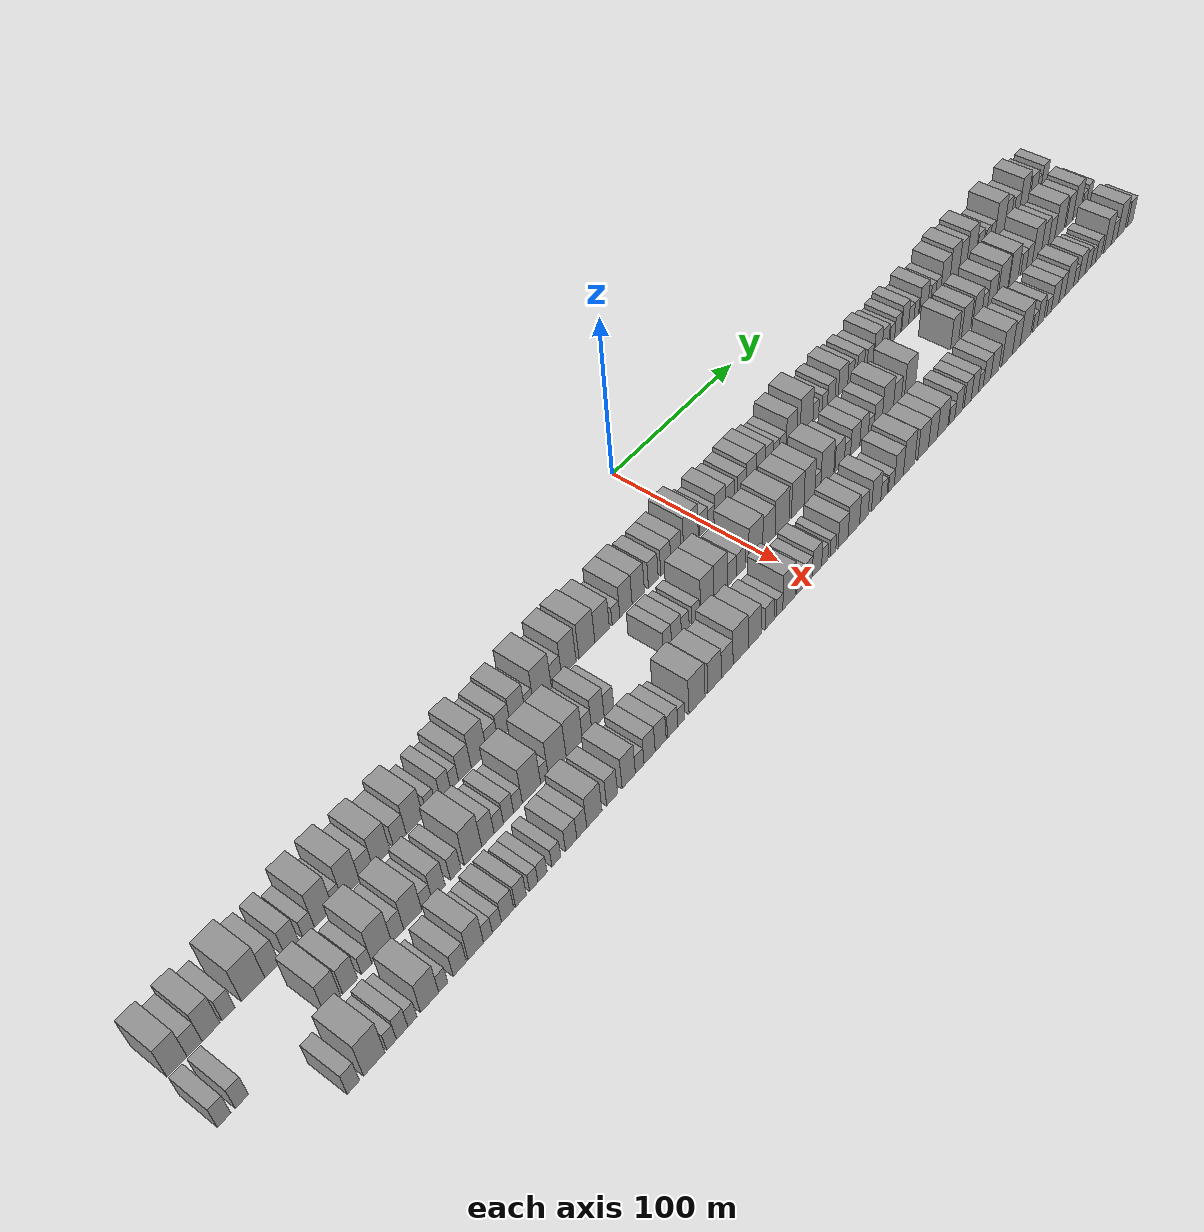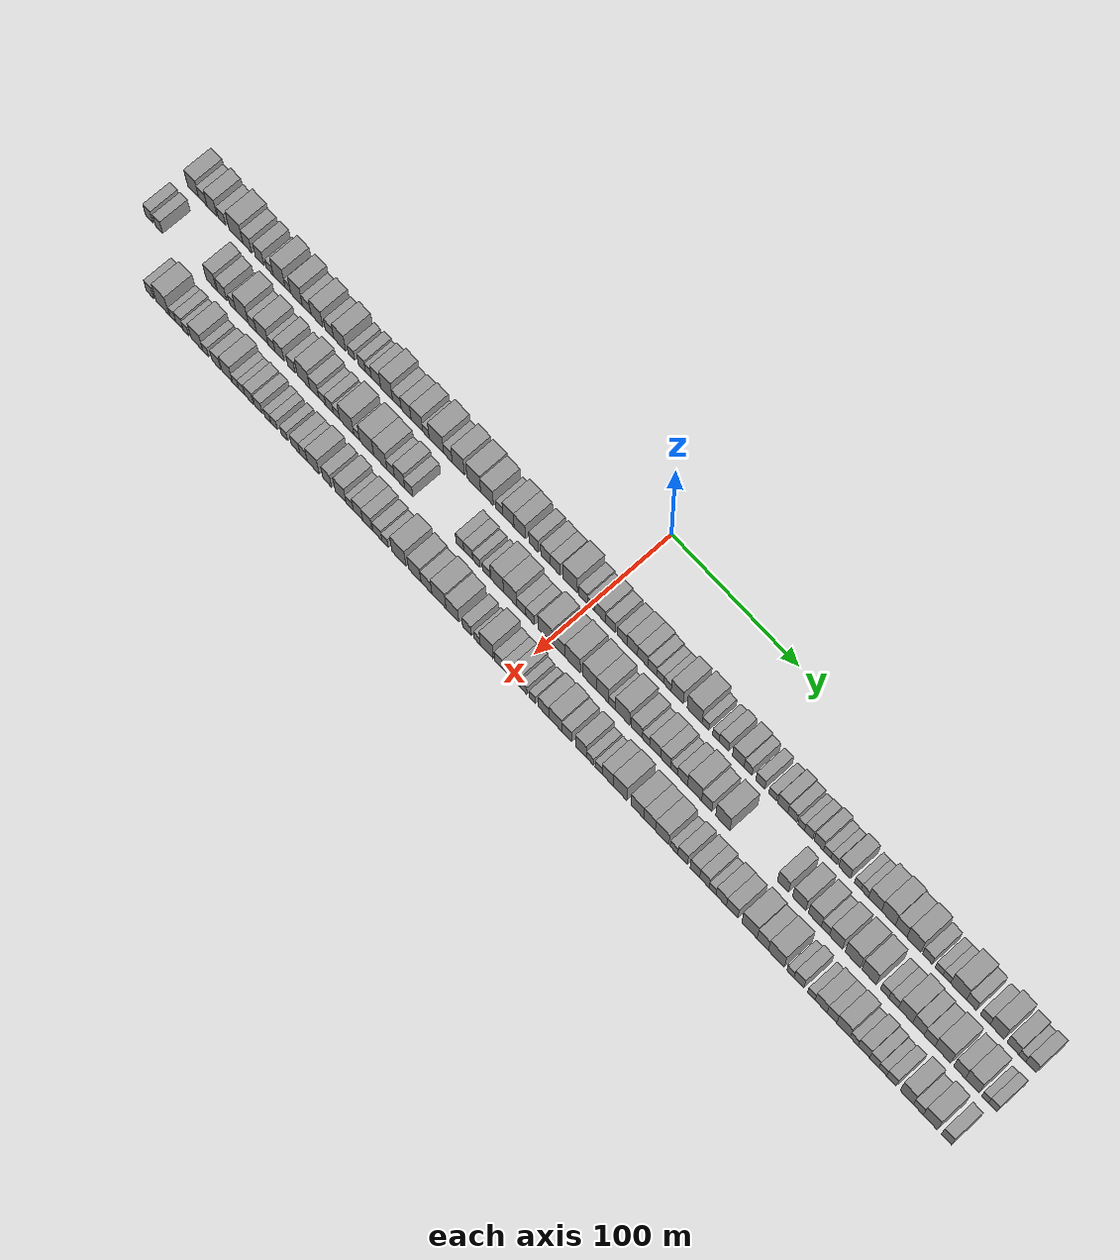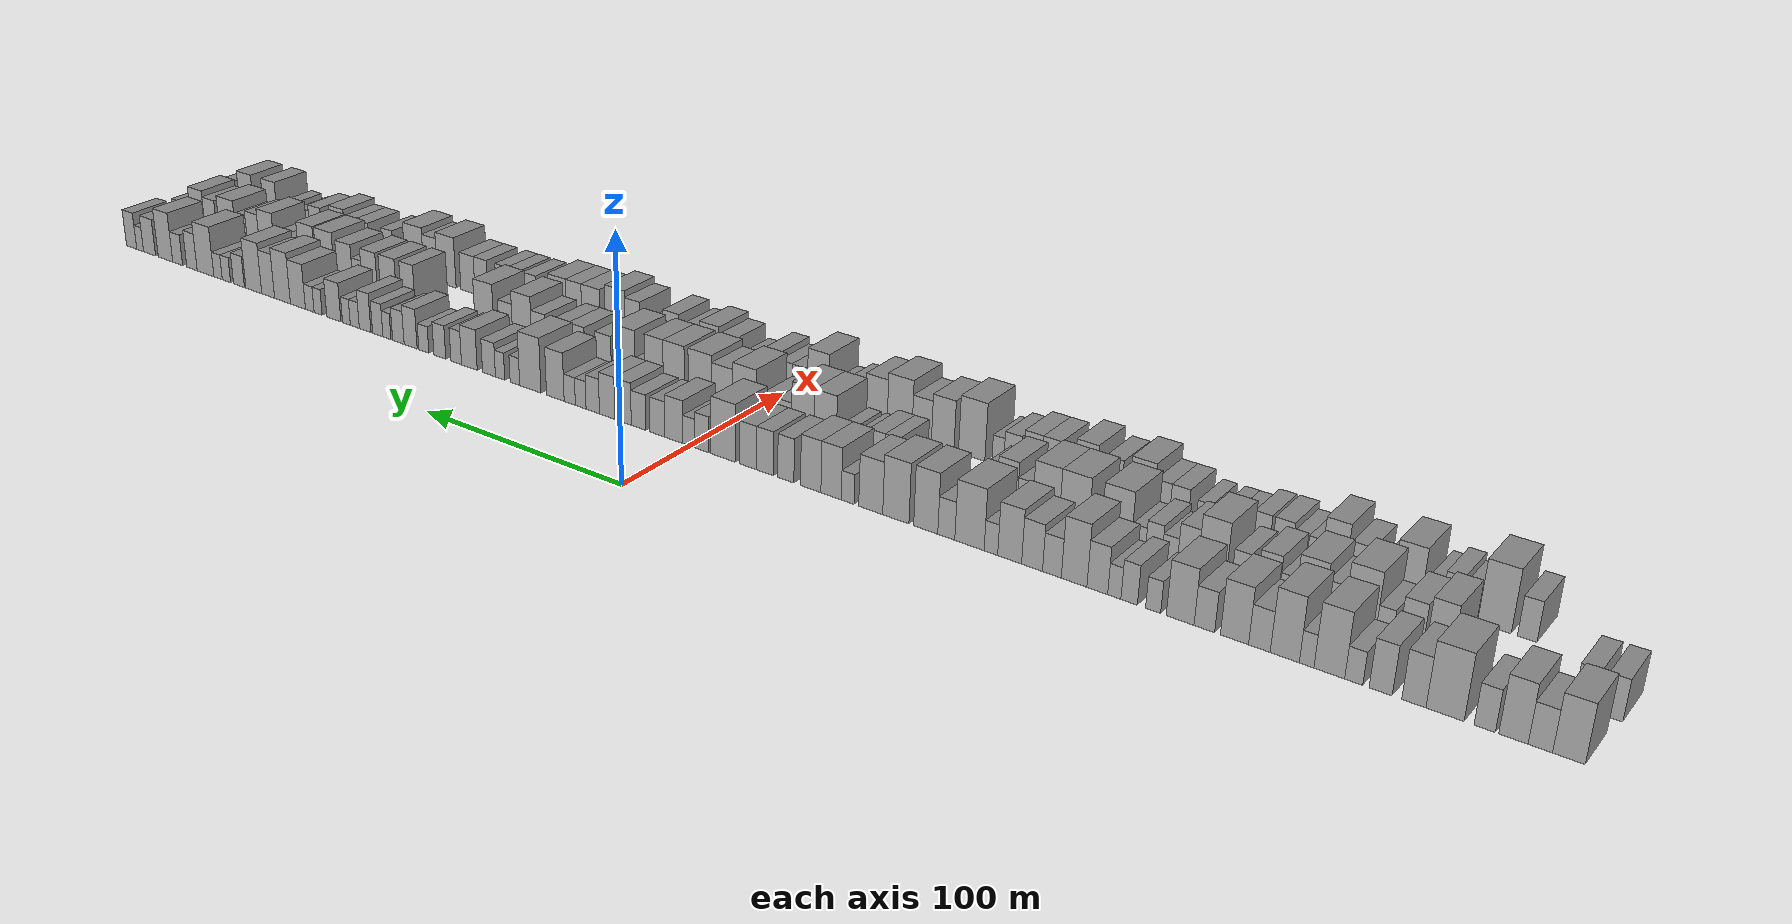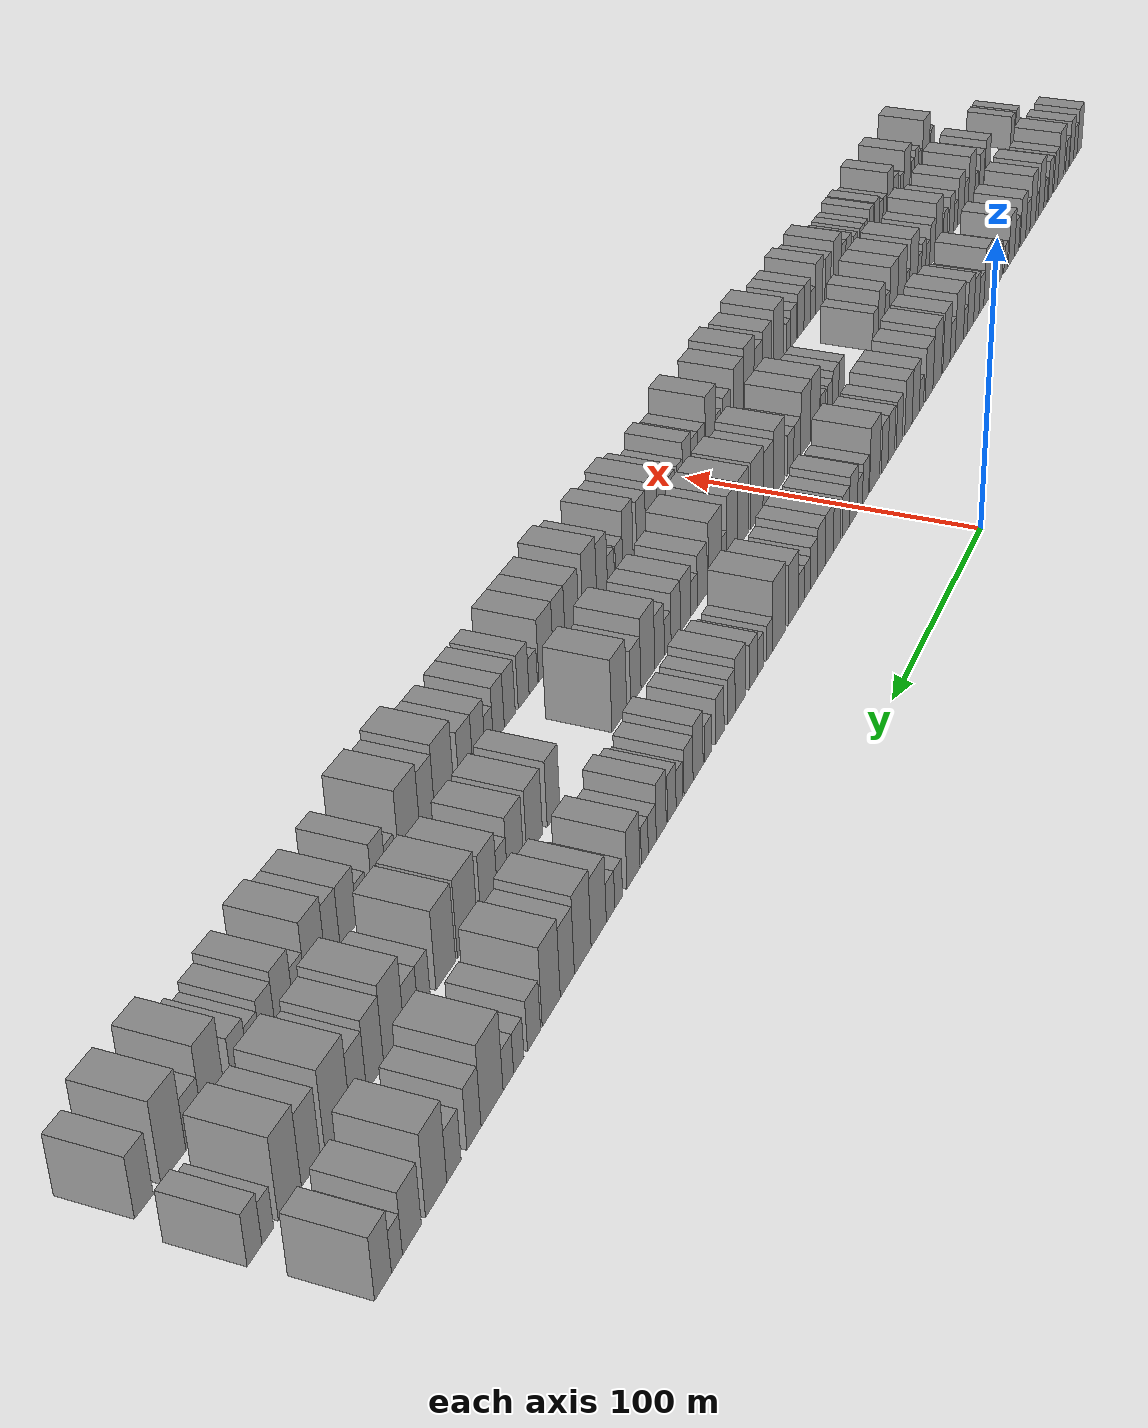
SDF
<sdf version="1.6">
 <world name="default">
  <scene>
   <sky><clouds><speed>12</speed></clouds></sky>
   <ambient>0.4 0.4 0.4 1</ambient>
   <background>0.7 0.7 0.7 1</background>
   <shadows>1</shadows>
  </scene>
  <gravity>0 0 -9.8066</gravity>
  <magnetic_field>6e-06 2.3e-05 -4.2e-05</magnetic_field>
  <physics default="0" name="default_physics" type="ode">
   <ode>
    <solver>
     <type>quick</type>
     <iters>10</iters>
     <sor>1.0</sor>
     <use_dynamic_moi_rescaling>0</use_dynamic_moi_rescaling>
    </solver>
    <constraints>
     <cfm>0</cfm>
     <erp>0.2</erp>
     <contact_max_correcting_vel>100</contact_max_correcting_vel>
     <contact_surface_layer>0.001</contact_surface_layer>
    </constraints>
   </ode>
   <max_step_size>0.004</max_step_size>
   <real_time_factor>1</real_time_factor>
   <real_time_update_rate>250</real_time_update_rate>
  </physics>
  <light name="sun" type="directional">
   <pose>0 0 10 0 0 0</pose>
   <diffuse>0.8 0.8 0.8 1</diffuse>
   <specular>0.2 0.2 0.2 1</specular>
   <attenuation>
    <range>1000</range>
    <constant>0.9</constant>
    <linear>0.01</linear>
    <quadratic>0.001</quadratic>
   </attenuation>
   <direction>-0.5 0.1 -0.9</direction>
  </light>
  <model name="building_1">
   <static>1</static>
   <pose>50.0000 -329.2814 0 0.000000 0.000000 0.000000</pose>
   <link name="link">
    <pose>0 0 10.50 0 0 0</pose>
    <collision name="collision"><geometry><box><size>20.0000 9.4373 21.0000</size></box></geometry></collision>
    <visual name="visual">
     <cast_shadows>0</cast_shadows>
     <geometry><box><size>20.0000 9.4373 21.0000</size></box></geometry>
     <material>
      <script>
       <uri>model://grey_wall/materials/scripts</uri>
       <uri>model://grey_wall/materials/textures</uri>
       <name>vrc/grey_wall</name>
      </script>
     </material>
    </visual>
   </link>
  </model>
  <model name="building_2">
   <static>1</static>
   <pose>50.0000 -320.9805 0 0.000000 0.000000 0.000000</pose>
   <link name="link">
    <pose>0 0 7.50 0 0 0</pose>
    <collision name="collision"><geometry><box><size>20.0000 7.1644 15.0000</size></box></geometry></collision>
    <visual name="visual">
     <cast_shadows>0</cast_shadows>
     <geometry><box><size>20.0000 7.1644 15.0000</size></box></geometry>
     <material>
      <script>
       <uri>model://grey_wall/materials/scripts</uri>
       <uri>model://grey_wall/materials/textures</uri>
       <name>vrc/grey_wall</name>
      </script>
     </material>
    </visual>
   </link>
  </model>
  <model name="building_3">
   <static>1</static>
   <pose>50.0000 -313.0436 0 0.000000 0.000000 0.000000</pose>
   <link name="link">
    <pose>0 0 10.50 0 0 0</pose>
    <collision name="collision"><geometry><box><size>20.0000 8.7095 21.0000</size></box></geometry></collision>
    <visual name="visual">
     <cast_shadows>0</cast_shadows>
     <geometry><box><size>20.0000 8.7095 21.0000</size></box></geometry>
     <material>
      <script>
       <uri>model://grey_wall/materials/scripts</uri>
       <uri>model://grey_wall/materials/textures</uri>
       <name>vrc/grey_wall</name>
      </script>
     </material>
    </visual>
   </link>
  </model>
  <model name="building_4">
   <static>1</static>
   <pose>50.0000 -304.4824 0 0.000000 0.000000 0.000000</pose>
   <link name="link">
    <pose>0 0 7.50 0 0 0</pose>
    <collision name="collision"><geometry><box><size>20.0000 6.4129 15.0000</size></box></geometry></collision>
    <visual name="visual">
     <cast_shadows>0</cast_shadows>
     <geometry><box><size>20.0000 6.4129 15.0000</size></box></geometry>
     <material>
      <script>
       <uri>model://grey_wall/materials/scripts</uri>
       <uri>model://grey_wall/materials/textures</uri>
       <name>vrc/grey_wall</name>
      </script>
     </material>
    </visual>
   </link>
  </model>
  <model name="building_5">
   <static>1</static>
   <pose>50.0000 -292.3860 0 0.000000 0.000000 0.000000</pose>
   <link name="link">
    <pose>0 0 12.00 0 0 0</pose>
    <collision name="collision"><geometry><box><size>20.0000 11.7800 24.0000</size></box></geometry></collision>
    <visual name="visual">
     <cast_shadows>0</cast_shadows>
     <geometry><box><size>20.0000 11.7800 24.0000</size></box></geometry>
     <material>
      <script>
       <uri>model://grey_wall/materials/scripts</uri>
       <uri>model://grey_wall/materials/textures</uri>
       <name>vrc/grey_wall</name>
      </script>
     </material>
    </visual>
   </link>
  </model>
  <model name="building_6">
   <static>1</static>
   <pose>50.0000 -282.7024 0 0.000000 0.000000 0.000000</pose>
   <link name="link">
    <pose>0 0 9.00 0 0 0</pose>
    <collision name="collision"><geometry><box><size>20.0000 7.5872 18.0000</size></box></geometry></collision>
    <visual name="visual">
     <cast_shadows>0</cast_shadows>
     <geometry><box><size>20.0000 7.5872 18.0000</size></box></geometry>
     <material>
      <script>
       <uri>model://grey_wall/materials/scripts</uri>
       <uri>model://grey_wall/materials/textures</uri>
       <name>vrc/grey_wall</name>
      </script>
     </material>
    </visual>
   </link>
  </model>
  <model name="building_7">
   <static>1</static>
   <pose>50.0000 -272.2078 0 0.000000 0.000000 0.000000</pose>
   <link name="link">
    <pose>0 0 9.00 0 0 0</pose>
    <collision name="collision"><geometry><box><size>20.0000 7.4020 18.0000</size></box></geometry></collision>
    <visual name="visual">
     <cast_shadows>0</cast_shadows>
     <geometry><box><size>20.0000 7.4020 18.0000</size></box></geometry>
     <material>
      <script>
       <uri>model://grey_wall/materials/scripts</uri>
       <uri>model://grey_wall/materials/textures</uri>
       <name>vrc/grey_wall</name>
      </script>
     </material>
    </visual>
   </link>
  </model>
  <model name="building_8">
   <static>1</static>
   <pose>50.0000 -263.5721 0 0.000000 0.000000 0.000000</pose>
   <link name="link">
    <pose>0 0 6.00 0 0 0</pose>
    <collision name="collision"><geometry><box><size>20.0000 5.8693 12.0000</size></box></geometry></collision>
    <visual name="visual">
     <cast_shadows>0</cast_shadows>
     <geometry><box><size>20.0000 5.8693 12.0000</size></box></geometry>
     <material>
      <script>
       <uri>model://grey_wall/materials/scripts</uri>
       <uri>model://grey_wall/materials/textures</uri>
       <name>vrc/grey_wall</name>
      </script>
     </material>
    </visual>
   </link>
  </model>
  <model name="building_9">
   <static>1</static>
   <pose>50.0000 -255.5919 0 0.000000 0.000000 0.000000</pose>
   <link name="link">
    <pose>0 0 12.00 0 0 0</pose>
    <collision name="collision"><geometry><box><size>20.0000 10.0912 24.0000</size></box></geometry></collision>
    <visual name="visual">
     <cast_shadows>0</cast_shadows>
     <geometry><box><size>20.0000 10.0912 24.0000</size></box></geometry>
     <material>
      <script>
       <uri>model://grey_wall/materials/scripts</uri>
       <uri>model://grey_wall/materials/textures</uri>
       <name>vrc/grey_wall</name>
      </script>
     </material>
    </visual>
   </link>
  </model>
  <model name="building_10">
   <static>1</static>
   <pose>50.0000 -248.1184 0 0.000000 0.000000 0.000000</pose>
   <link name="link">
    <pose>0 0 6.00 0 0 0</pose>
    <collision name="collision"><geometry><box><size>20.0000 4.8559 12.0000</size></box></geometry></collision>
    <visual name="visual">
     <cast_shadows>0</cast_shadows>
     <geometry><box><size>20.0000 4.8559 12.0000</size></box></geometry>
     <material>
      <script>
       <uri>model://grey_wall/materials/scripts</uri>
       <uri>model://grey_wall/materials/textures</uri>
       <name>vrc/grey_wall</name>
      </script>
     </material>
    </visual>
   </link>
  </model>
  <model name="building_11">
   <static>1</static>
   <pose>50.0000 -240.7936 0 0.000000 0.000000 0.000000</pose>
   <link name="link">
    <pose>0 0 12.00 0 0 0</pose>
    <collision name="collision"><geometry><box><size>20.0000 9.7935 24.0000</size></box></geometry></collision>
    <visual name="visual">
     <cast_shadows>0</cast_shadows>
     <geometry><box><size>20.0000 9.7935 24.0000</size></box></geometry>
     <material>
      <script>
       <uri>model://grey_wall/materials/scripts</uri>
       <uri>model://grey_wall/materials/textures</uri>
       <name>vrc/grey_wall</name>
      </script>
     </material>
    </visual>
   </link>
  </model>
  <model name="building_12">
   <static>1</static>
   <pose>50.0000 -232.1955 0 0.000000 0.000000 0.000000</pose>
   <link name="link">
    <pose>0 0 7.50 0 0 0</pose>
    <collision name="collision"><geometry><box><size>20.0000 7.4026 15.0000</size></box></geometry></collision>
    <visual name="visual">
     <cast_shadows>0</cast_shadows>
     <geometry><box><size>20.0000 7.4026 15.0000</size></box></geometry>
     <material>
      <script>
       <uri>model://grey_wall/materials/scripts</uri>
       <uri>model://grey_wall/materials/textures</uri>
       <name>vrc/grey_wall</name>
      </script>
     </material>
    </visual>
   </link>
  </model>
  <model name="building_13">
   <static>1</static>
   <pose>50.0000 -223.6190 0 0.000000 0.000000 0.000000</pose>
   <link name="link">
    <pose>0 0 10.50 0 0 0</pose>
    <collision name="collision"><geometry><box><size>20.0000 9.7504 21.0000</size></box></geometry></collision>
    <visual name="visual">
     <cast_shadows>0</cast_shadows>
     <geometry><box><size>20.0000 9.7504 21.0000</size></box></geometry>
     <material>
      <script>
       <uri>model://grey_wall/materials/scripts</uri>
       <uri>model://grey_wall/materials/textures</uri>
       <name>vrc/grey_wall</name>
      </script>
     </material>
    </visual>
   </link>
  </model>
  <model name="building_14">
   <static>1</static>
   <pose>50.0000 -213.1041 0 0.000000 0.000000 0.000000</pose>
   <link name="link">
    <pose>0 0 7.50 0 0 0</pose>
    <collision name="collision"><geometry><box><size>20.0000 7.2796 15.0000</size></box></geometry></collision>
    <visual name="visual">
     <cast_shadows>0</cast_shadows>
     <geometry><box><size>20.0000 7.2796 15.0000</size></box></geometry>
     <material>
      <script>
       <uri>model://grey_wall/materials/scripts</uri>
       <uri>model://grey_wall/materials/textures</uri>
       <name>vrc/grey_wall</name>
      </script>
     </material>
    </visual>
   </link>
  </model>
  <model name="building_15">
   <static>1</static>
   <pose>50.0000 -204.4981 0 0.000000 0.000000 0.000000</pose>
   <link name="link">
    <pose>0 0 10.50 0 0 0</pose>
    <collision name="collision"><geometry><box><size>20.0000 9.9324 21.0000</size></box></geometry></collision>
    <visual name="visual">
     <cast_shadows>0</cast_shadows>
     <geometry><box><size>20.0000 9.9324 21.0000</size></box></geometry>
     <material>
      <script>
       <uri>model://grey_wall/materials/scripts</uri>
       <uri>model://grey_wall/materials/textures</uri>
       <name>vrc/grey_wall</name>
      </script>
     </material>
    </visual>
   </link>
  </model>
  <model name="building_16">
   <static>1</static>
   <pose>50.0000 -194.7910 0 0.000000 0.000000 0.000000</pose>
   <link name="link">
    <pose>0 0 6.00 0 0 0</pose>
    <collision name="collision"><geometry><box><size>20.0000 5.4818 12.0000</size></box></geometry></collision>
    <visual name="visual">
     <cast_shadows>0</cast_shadows>
     <geometry><box><size>20.0000 5.4818 12.0000</size></box></geometry>
     <material>
      <script>
       <uri>model://grey_wall/materials/scripts</uri>
       <uri>model://grey_wall/materials/textures</uri>
       <name>vrc/grey_wall</name>
      </script>
     </material>
    </visual>
   </link>
  </model>
  <model name="building_17">
   <static>1</static>
   <pose>50.0000 -186.0106 0 0.000000 0.000000 0.000000</pose>
   <link name="link">
    <pose>0 0 7.50 0 0 0</pose>
    <collision name="collision"><geometry><box><size>20.0000 6.0790 15.0000</size></box></geometry></collision>
    <visual name="visual">
     <cast_shadows>0</cast_shadows>
     <geometry><box><size>20.0000 6.0790 15.0000</size></box></geometry>
     <material>
      <script>
       <uri>model://grey_wall/materials/scripts</uri>
       <uri>model://grey_wall/materials/textures</uri>
       <name>vrc/grey_wall</name>
      </script>
     </material>
    </visual>
   </link>
  </model>
  <model name="building_18">
   <static>1</static>
   <pose>50.0000 -180.5212 0 0.000000 0.000000 0.000000</pose>
   <link name="link">
    <pose>0 0 6.00 0 0 0</pose>
    <collision name="collision"><geometry><box><size>20.0000 4.8997 12.0000</size></box></geometry></collision>
    <visual name="visual">
     <cast_shadows>0</cast_shadows>
     <geometry><box><size>20.0000 4.8997 12.0000</size></box></geometry>
     <material>
      <script>
       <uri>model://grey_wall/materials/scripts</uri>
       <uri>model://grey_wall/materials/textures</uri>
       <name>vrc/grey_wall</name>
      </script>
     </material>
    </visual>
   </link>
  </model>
  <model name="building_19">
   <static>1</static>
   <pose>50.0000 -174.1651 0 0.000000 0.000000 0.000000</pose>
   <link name="link">
    <pose>0 0 9.00 0 0 0</pose>
    <collision name="collision"><geometry><box><size>20.0000 7.8126 18.0000</size></box></geometry></collision>
    <visual name="visual">
     <cast_shadows>0</cast_shadows>
     <geometry><box><size>20.0000 7.8126 18.0000</size></box></geometry>
     <material>
      <script>
       <uri>model://grey_wall/materials/scripts</uri>
       <uri>model://grey_wall/materials/textures</uri>
       <name>vrc/grey_wall</name>
      </script>
     </material>
    </visual>
   </link>
  </model>
  <model name="building_20">
   <static>1</static>
   <pose>50.0000 -165.3733 0 0.000000 0.000000 0.000000</pose>
   <link name="link">
    <pose>0 0 12.00 0 0 0</pose>
    <collision name="collision"><geometry><box><size>20.0000 9.7710 24.0000</size></box></geometry></collision>
    <visual name="visual">
     <cast_shadows>0</cast_shadows>
     <geometry><box><size>20.0000 9.7710 24.0000</size></box></geometry>
     <material>
      <script>
       <uri>model://grey_wall/materials/scripts</uri>
       <uri>model://grey_wall/materials/textures</uri>
       <name>vrc/grey_wall</name>
      </script>
     </material>
    </visual>
   </link>
  </model>
  <model name="building_21">
   <static>1</static>
   <pose>50.0000 -156.8702 0 0.000000 0.000000 0.000000</pose>
   <link name="link">
    <pose>0 0 7.50 0 0 0</pose>
    <collision name="collision"><geometry><box><size>20.0000 7.2352 15.0000</size></box></geometry></collision>
    <visual name="visual">
     <cast_shadows>0</cast_shadows>
     <geometry><box><size>20.0000 7.2352 15.0000</size></box></geometry>
     <material>
      <script>
       <uri>model://grey_wall/materials/scripts</uri>
       <uri>model://grey_wall/materials/textures</uri>
       <name>vrc/grey_wall</name>
      </script>
     </material>
    </visual>
   </link>
  </model>
  <model name="building_22">
   <static>1</static>
   <pose>50.0000 -149.1597 0 0.000000 0.000000 0.000000</pose>
   <link name="link">
    <pose>0 0 9.00 0 0 0</pose>
    <collision name="collision"><geometry><box><size>20.0000 8.1858 18.0000</size></box></geometry></collision>
    <visual name="visual">
     <cast_shadows>0</cast_shadows>
     <geometry><box><size>20.0000 8.1858 18.0000</size></box></geometry>
     <material>
      <script>
       <uri>model://grey_wall/materials/scripts</uri>
       <uri>model://grey_wall/materials/textures</uri>
       <name>vrc/grey_wall</name>
      </script>
     </material>
    </visual>
   </link>
  </model>
  <model name="building_23">
   <static>1</static>
   <pose>50.0000 -140.3261 0 0.000000 0.000000 0.000000</pose>
   <link name="link">
    <pose>0 0 10.50 0 0 0</pose>
    <collision name="collision"><geometry><box><size>20.0000 9.4813 21.0000</size></box></geometry></collision>
    <visual name="visual">
     <cast_shadows>0</cast_shadows>
     <geometry><box><size>20.0000 9.4813 21.0000</size></box></geometry>
     <material>
      <script>
       <uri>model://grey_wall/materials/scripts</uri>
       <uri>model://grey_wall/materials/textures</uri>
       <name>vrc/grey_wall</name>
      </script>
     </material>
    </visual>
   </link>
  </model>
  <model name="building_24">
   <static>1</static>
   <pose>50.0000 -132.8740 0 0.000000 0.000000 0.000000</pose>
   <link name="link">
    <pose>0 0 6.00 0 0 0</pose>
    <collision name="collision"><geometry><box><size>20.0000 5.4228 12.0000</size></box></geometry></collision>
    <visual name="visual">
     <cast_shadows>0</cast_shadows>
     <geometry><box><size>20.0000 5.4228 12.0000</size></box></geometry>
     <material>
      <script>
       <uri>model://grey_wall/materials/scripts</uri>
       <uri>model://grey_wall/materials/textures</uri>
       <name>vrc/grey_wall</name>
      </script>
     </material>
    </visual>
   </link>
  </model>
  <model name="building_25">
   <static>1</static>
   <pose>50.0000 -124.2080 0 0.000000 0.000000 0.000000</pose>
   <link name="link">
    <pose>0 0 12.00 0 0 0</pose>
    <collision name="collision"><geometry><box><size>20.0000 11.9093 24.0000</size></box></geometry></collision>
    <visual name="visual">
     <cast_shadows>0</cast_shadows>
     <geometry><box><size>20.0000 11.9093 24.0000</size></box></geometry>
     <material>
      <script>
       <uri>model://grey_wall/materials/scripts</uri>
       <uri>model://grey_wall/materials/textures</uri>
       <name>vrc/grey_wall</name>
      </script>
     </material>
    </visual>
   </link>
  </model>
  <model name="building_26">
   <static>1</static>
   <pose>50.0000 -114.7484 0 0.000000 0.000000 0.000000</pose>
   <link name="link">
    <pose>0 0 7.50 0 0 0</pose>
    <collision name="collision"><geometry><box><size>20.0000 7.0100 15.0000</size></box></geometry></collision>
    <visual name="visual">
     <cast_shadows>0</cast_shadows>
     <geometry><box><size>20.0000 7.0100 15.0000</size></box></geometry>
     <material>
      <script>
       <uri>model://grey_wall/materials/scripts</uri>
       <uri>model://grey_wall/materials/textures</uri>
       <name>vrc/grey_wall</name>
      </script>
     </material>
    </visual>
   </link>
  </model>
  <model name="building_27">
   <static>1</static>
   <pose>50.0000 -106.2114 0 0.000000 0.000000 0.000000</pose>
   <link name="link">
    <pose>0 0 12.00 0 0 0</pose>
    <collision name="collision"><geometry><box><size>20.0000 10.0640 24.0000</size></box></geometry></collision>
    <visual name="visual">
     <cast_shadows>0</cast_shadows>
     <geometry><box><size>20.0000 10.0640 24.0000</size></box></geometry>
     <material>
      <script>
       <uri>model://grey_wall/materials/scripts</uri>
       <uri>model://grey_wall/materials/textures</uri>
       <name>vrc/grey_wall</name>
      </script>
     </material>
    </visual>
   </link>
  </model>
  <model name="building_28">
   <static>1</static>
   <pose>50.0000 -93.5973 0 0.000000 0.000000 0.000000</pose>
   <link name="link">
    <pose>0 0 12.00 0 0 0</pose>
    <collision name="collision"><geometry><box><size>20.0000 11.1640 24.0000</size></box></geometry></collision>
    <visual name="visual">
     <cast_shadows>0</cast_shadows>
     <geometry><box><size>20.0000 11.1640 24.0000</size></box></geometry>
     <material>
      <script>
       <uri>model://grey_wall/materials/scripts</uri>
       <uri>model://grey_wall/materials/textures</uri>
       <name>vrc/grey_wall</name>
      </script>
     </material>
    </visual>
   </link>
  </model>
  <model name="building_29">
   <static>1</static>
   <pose>50.0000 -82.8257 0 0.000000 0.000000 0.000000</pose>
   <link name="link">
    <pose>0 0 10.50 0 0 0</pose>
    <collision name="collision"><geometry><box><size>20.0000 10.3791 21.0000</size></box></geometry></collision>
    <visual name="visual">
     <cast_shadows>0</cast_shadows>
     <geometry><box><size>20.0000 10.3791 21.0000</size></box></geometry>
     <material>
      <script>
       <uri>model://grey_wall/materials/scripts</uri>
       <uri>model://grey_wall/materials/textures</uri>
       <name>vrc/grey_wall</name>
      </script>
     </material>
    </visual>
   </link>
  </model>
  <model name="building_30">
   <static>1</static>
   <pose>50.0000 -72.8177 0 0.000000 0.000000 0.000000</pose>
   <link name="link">
    <pose>0 0 6.00 0 0 0</pose>
    <collision name="collision"><geometry><box><size>20.0000 5.6370 12.0000</size></box></geometry></collision>
    <visual name="visual">
     <cast_shadows>0</cast_shadows>
     <geometry><box><size>20.0000 5.6370 12.0000</size></box></geometry>
     <material>
      <script>
       <uri>model://grey_wall/materials/scripts</uri>
       <uri>model://grey_wall/materials/textures</uri>
       <name>vrc/grey_wall</name>
      </script>
     </material>
    </visual>
   </link>
  </model>
  <model name="building_31">
   <static>1</static>
   <pose>50.0000 -65.4718 0 0.000000 0.000000 0.000000</pose>
   <link name="link">
    <pose>0 0 10.50 0 0 0</pose>
    <collision name="collision"><geometry><box><size>20.0000 9.0548 21.0000</size></box></geometry></collision>
    <visual name="visual">
     <cast_shadows>0</cast_shadows>
     <geometry><box><size>20.0000 9.0548 21.0000</size></box></geometry>
     <material>
      <script>
       <uri>model://grey_wall/materials/scripts</uri>
       <uri>model://grey_wall/materials/textures</uri>
       <name>vrc/grey_wall</name>
      </script>
     </material>
    </visual>
   </link>
  </model>
  <model name="building_32">
   <static>1</static>
   <pose>50.0000 -56.3522 0 0.000000 0.000000 0.000000</pose>
   <link name="link">
    <pose>0 0 10.50 0 0 0</pose>
    <collision name="collision"><geometry><box><size>20.0000 9.1843 21.0000</size></box></geometry></collision>
    <visual name="visual">
     <cast_shadows>0</cast_shadows>
     <geometry><box><size>20.0000 9.1843 21.0000</size></box></geometry>
     <material>
      <script>
       <uri>model://grey_wall/materials/scripts</uri>
       <uri>model://grey_wall/materials/textures</uri>
       <name>vrc/grey_wall</name>
      </script>
     </material>
    </visual>
   </link>
  </model>
  <model name="building_33">
   <static>1</static>
   <pose>50.0000 -45.0540 0 0.000000 0.000000 0.000000</pose>
   <link name="link">
    <pose>0 0 9.00 0 0 0</pose>
    <collision name="collision"><geometry><box><size>20.0000 7.4122 18.0000</size></box></geometry></collision>
    <visual name="visual">
     <cast_shadows>0</cast_shadows>
     <geometry><box><size>20.0000 7.4122 18.0000</size></box></geometry>
     <material>
      <script>
       <uri>model://grey_wall/materials/scripts</uri>
       <uri>model://grey_wall/materials/textures</uri>
       <name>vrc/grey_wall</name>
      </script>
     </material>
    </visual>
   </link>
  </model>
  <model name="building_34">
   <static>1</static>
   <pose>50.0000 -35.4445 0 0.000000 0.000000 0.000000</pose>
   <link name="link">
    <pose>0 0 9.00 0 0 0</pose>
    <collision name="collision"><geometry><box><size>20.0000 7.8068 18.0000</size></box></geometry></collision>
    <visual name="visual">
     <cast_shadows>0</cast_shadows>
     <geometry><box><size>20.0000 7.8068 18.0000</size></box></geometry>
     <material>
      <script>
       <uri>model://grey_wall/materials/scripts</uri>
       <uri>model://grey_wall/materials/textures</uri>
       <name>vrc/grey_wall</name>
      </script>
     </material>
    </visual>
   </link>
  </model>
  <model name="building_35">
   <static>1</static>
   <pose>50.0000 -27.5929 0 0.000000 0.000000 0.000000</pose>
   <link name="link">
    <pose>0 0 9.00 0 0 0</pose>
    <collision name="collision"><geometry><box><size>20.0000 7.8964 18.0000</size></box></geometry></collision>
    <visual name="visual">
     <cast_shadows>0</cast_shadows>
     <geometry><box><size>20.0000 7.8964 18.0000</size></box></geometry>
     <material>
      <script>
       <uri>model://grey_wall/materials/scripts</uri>
       <uri>model://grey_wall/materials/textures</uri>
       <name>vrc/grey_wall</name>
      </script>
     </material>
    </visual>
   </link>
  </model>
  <model name="building_36">
   <static>1</static>
   <pose>50.0000 -15.8348 0 0.000000 0.000000 0.000000</pose>
   <link name="link">
    <pose>0 0 12.00 0 0 0</pose>
    <collision name="collision"><geometry><box><size>20.0000 11.6198 24.0000</size></box></geometry></collision>
    <visual name="visual">
     <cast_shadows>0</cast_shadows>
     <geometry><box><size>20.0000 11.6198 24.0000</size></box></geometry>
     <material>
      <script>
       <uri>model://grey_wall/materials/scripts</uri>
       <uri>model://grey_wall/materials/textures</uri>
       <name>vrc/grey_wall</name>
      </script>
     </material>
    </visual>
   </link>
  </model>
  <model name="building_37">
   <static>1</static>
   <pose>50.0000 -5.5532 0 0.000000 0.000000 0.000000</pose>
   <link name="link">
    <pose>0 0 7.50 0 0 0</pose>
    <collision name="collision"><geometry><box><size>20.0000 6.9434 15.0000</size></box></geometry></collision>
    <visual name="visual">
     <cast_shadows>0</cast_shadows>
     <geometry><box><size>20.0000 6.9434 15.0000</size></box></geometry>
     <material>
      <script>
       <uri>model://grey_wall/materials/scripts</uri>
       <uri>model://grey_wall/materials/textures</uri>
       <name>vrc/grey_wall</name>
      </script>
     </material>
    </visual>
   </link>
  </model>
  <model name="building_38">
   <static>1</static>
   <pose>50.0000 0.7761 0 0.000000 0.000000 0.000000</pose>
   <link name="link">
    <pose>0 0 6.00 0 0 0</pose>
    <collision name="collision"><geometry><box><size>20.0000 5.7152 12.0000</size></box></geometry></collision>
    <visual name="visual">
     <cast_shadows>0</cast_shadows>
     <geometry><box><size>20.0000 5.7152 12.0000</size></box></geometry>
     <material>
      <script>
       <uri>model://grey_wall/materials/scripts</uri>
       <uri>model://grey_wall/materials/textures</uri>
       <name>vrc/grey_wall</name>
      </script>
     </material>
    </visual>
   </link>
  </model>
  <model name="building_39">
   <static>1</static>
   <pose>50.0000 8.0830 0 0.000000 0.000000 0.000000</pose>
   <link name="link">
    <pose>0 0 9.00 0 0 0</pose>
    <collision name="collision"><geometry><box><size>20.0000 8.8988 18.0000</size></box></geometry></collision>
    <visual name="visual">
     <cast_shadows>0</cast_shadows>
     <geometry><box><size>20.0000 8.8988 18.0000</size></box></geometry>
     <material>
      <script>
       <uri>model://grey_wall/materials/scripts</uri>
       <uri>model://grey_wall/materials/textures</uri>
       <name>vrc/grey_wall</name>
      </script>
     </material>
    </visual>
   </link>
  </model>
  <model name="building_40">
   <static>1</static>
   <pose>50.0000 16.2663 0 0.000000 0.000000 0.000000</pose>
   <link name="link">
    <pose>0 0 7.50 0 0 0</pose>
    <collision name="collision"><geometry><box><size>20.0000 7.4677 15.0000</size></box></geometry></collision>
    <visual name="visual">
     <cast_shadows>0</cast_shadows>
     <geometry><box><size>20.0000 7.4677 15.0000</size></box></geometry>
     <material>
      <script>
       <uri>model://grey_wall/materials/scripts</uri>
       <uri>model://grey_wall/materials/textures</uri>
       <name>vrc/grey_wall</name>
      </script>
     </material>
    </visual>
   </link>
  </model>
  <model name="building_41">
   <static>1</static>
   <pose>50.0000 25.6822 0 0.000000 0.000000 0.000000</pose>
   <link name="link">
    <pose>0 0 7.50 0 0 0</pose>
    <collision name="collision"><geometry><box><size>20.0000 7.3641 15.0000</size></box></geometry></collision>
    <visual name="visual">
     <cast_shadows>0</cast_shadows>
     <geometry><box><size>20.0000 7.3641 15.0000</size></box></geometry>
     <material>
      <script>
       <uri>model://grey_wall/materials/scripts</uri>
       <uri>model://grey_wall/materials/textures</uri>
       <name>vrc/grey_wall</name>
      </script>
     </material>
    </visual>
   </link>
  </model>
  <model name="building_42">
   <static>1</static>
   <pose>50.0000 33.5626 0 0.000000 0.000000 0.000000</pose>
   <link name="link">
    <pose>0 0 9.00 0 0 0</pose>
    <collision name="collision"><geometry><box><size>20.0000 8.3966 18.0000</size></box></geometry></collision>
    <visual name="visual">
     <cast_shadows>0</cast_shadows>
     <geometry><box><size>20.0000 8.3966 18.0000</size></box></geometry>
     <material>
      <script>
       <uri>model://grey_wall/materials/scripts</uri>
       <uri>model://grey_wall/materials/textures</uri>
       <name>vrc/grey_wall</name>
      </script>
     </material>
    </visual>
   </link>
  </model>
  <model name="building_43">
   <static>1</static>
   <pose>50.0000 41.7393 0 0.000000 0.000000 0.000000</pose>
   <link name="link">
    <pose>0 0 9.00 0 0 0</pose>
    <collision name="collision"><geometry><box><size>20.0000 7.9568 18.0000</size></box></geometry></collision>
    <visual name="visual">
     <cast_shadows>0</cast_shadows>
     <geometry><box><size>20.0000 7.9568 18.0000</size></box></geometry>
     <material>
      <script>
       <uri>model://grey_wall/materials/scripts</uri>
       <uri>model://grey_wall/materials/textures</uri>
       <name>vrc/grey_wall</name>
      </script>
     </material>
    </visual>
   </link>
  </model>
  <model name="building_44">
   <static>1</static>
   <pose>50.0000 49.2148 0 0.000000 0.000000 0.000000</pose>
   <link name="link">
    <pose>0 0 7.50 0 0 0</pose>
    <collision name="collision"><geometry><box><size>20.0000 6.9943 15.0000</size></box></geometry></collision>
    <visual name="visual">
     <cast_shadows>0</cast_shadows>
     <geometry><box><size>20.0000 6.9943 15.0000</size></box></geometry>
     <material>
      <script>
       <uri>model://grey_wall/materials/scripts</uri>
       <uri>model://grey_wall/materials/textures</uri>
       <name>vrc/grey_wall</name>
      </script>
     </material>
    </visual>
   </link>
  </model>
  <model name="building_45">
   <static>1</static>
   <pose>50.0000 55.5354 0 0.000000 0.000000 0.000000</pose>
   <link name="link">
    <pose>0 0 6.00 0 0 0</pose>
    <collision name="collision"><geometry><box><size>20.0000 5.6469 12.0000</size></box></geometry></collision>
    <visual name="visual">
     <cast_shadows>0</cast_shadows>
     <geometry><box><size>20.0000 5.6469 12.0000</size></box></geometry>
     <material>
      <script>
       <uri>model://grey_wall/materials/scripts</uri>
       <uri>model://grey_wall/materials/textures</uri>
       <name>vrc/grey_wall</name>
      </script>
     </material>
    </visual>
   </link>
  </model>
  <model name="building_46">
   <static>1</static>
   <pose>50.0000 61.3290 0 0.000000 0.000000 0.000000</pose>
   <link name="link">
    <pose>0 0 6.00 0 0 0</pose>
    <collision name="collision"><geometry><box><size>20.0000 5.9403 12.0000</size></box></geometry></collision>
    <visual name="visual">
     <cast_shadows>0</cast_shadows>
     <geometry><box><size>20.0000 5.9403 12.0000</size></box></geometry>
     <material>
      <script>
       <uri>model://grey_wall/materials/scripts</uri>
       <uri>model://grey_wall/materials/textures</uri>
       <name>vrc/grey_wall</name>
      </script>
     </material>
    </visual>
   </link>
  </model>
  <model name="building_47">
   <static>1</static>
   <pose>50.0000 69.0229 0 0.000000 0.000000 0.000000</pose>
   <link name="link">
    <pose>0 0 10.50 0 0 0</pose>
    <collision name="collision"><geometry><box><size>20.0000 9.4476 21.0000</size></box></geometry></collision>
    <visual name="visual">
     <cast_shadows>0</cast_shadows>
     <geometry><box><size>20.0000 9.4476 21.0000</size></box></geometry>
     <material>
      <script>
       <uri>model://grey_wall/materials/scripts</uri>
       <uri>model://grey_wall/materials/textures</uri>
       <name>vrc/grey_wall</name>
      </script>
     </material>
    </visual>
   </link>
  </model>
  <model name="building_48">
   <static>1</static>
   <pose>50.0000 82.5498 0 0.000000 0.000000 0.000000</pose>
   <link name="link">
    <pose>0 0 12.00 0 0 0</pose>
    <collision name="collision"><geometry><box><size>20.0000 11.6061 24.0000</size></box></geometry></collision>
    <visual name="visual">
     <cast_shadows>0</cast_shadows>
     <geometry><box><size>20.0000 11.6061 24.0000</size></box></geometry>
     <material>
      <script>
       <uri>model://grey_wall/materials/scripts</uri>
       <uri>model://grey_wall/materials/textures</uri>
       <name>vrc/grey_wall</name>
      </script>
     </material>
    </visual>
   </link>
  </model>
  <model name="building_49">
   <static>1</static>
   <pose>50.0000 90.9931 0 0.000000 0.000000 0.000000</pose>
   <link name="link">
    <pose>0 0 6.00 0 0 0</pose>
    <collision name="collision"><geometry><box><size>20.0000 5.2807 12.0000</size></box></geometry></collision>
    <visual name="visual">
     <cast_shadows>0</cast_shadows>
     <geometry><box><size>20.0000 5.2807 12.0000</size></box></geometry>
     <material>
      <script>
       <uri>model://grey_wall/materials/scripts</uri>
       <uri>model://grey_wall/materials/textures</uri>
       <name>vrc/grey_wall</name>
      </script>
     </material>
    </visual>
   </link>
  </model>
  <model name="building_50">
   <static>1</static>
   <pose>50.0000 99.2184 0 0.000000 0.000000 0.000000</pose>
   <link name="link">
    <pose>0 0 6.00 0 0 0</pose>
    <collision name="collision"><geometry><box><size>20.0000 5.1699 12.0000</size></box></geometry></collision>
    <visual name="visual">
     <cast_shadows>0</cast_shadows>
     <geometry><box><size>20.0000 5.1699 12.0000</size></box></geometry>
     <material>
      <script>
       <uri>model://grey_wall/materials/scripts</uri>
       <uri>model://grey_wall/materials/textures</uri>
       <name>vrc/grey_wall</name>
      </script>
     </material>
    </visual>
   </link>
  </model>
  <model name="building_51">
   <static>1</static>
   <pose>50.0000 105.4451 0 0.000000 0.000000 0.000000</pose>
   <link name="link">
    <pose>0 0 7.50 0 0 0</pose>
    <collision name="collision"><geometry><box><size>20.0000 7.2834 15.0000</size></box></geometry></collision>
    <visual name="visual">
     <cast_shadows>0</cast_shadows>
     <geometry><box><size>20.0000 7.2834 15.0000</size></box></geometry>
     <material>
      <script>
       <uri>model://grey_wall/materials/scripts</uri>
       <uri>model://grey_wall/materials/textures</uri>
       <name>vrc/grey_wall</name>
      </script>
     </material>
    </visual>
   </link>
  </model>
  <model name="building_52">
   <static>1</static>
   <pose>50.0000 116.5510 0 0.000000 0.000000 0.000000</pose>
   <link name="link">
    <pose>0 0 9.00 0 0 0</pose>
    <collision name="collision"><geometry><box><size>20.0000 8.9284 18.0000</size></box></geometry></collision>
    <visual name="visual">
     <cast_shadows>0</cast_shadows>
     <geometry><box><size>20.0000 8.9284 18.0000</size></box></geometry>
     <material>
      <script>
       <uri>model://grey_wall/materials/scripts</uri>
       <uri>model://grey_wall/materials/textures</uri>
       <name>vrc/grey_wall</name>
      </script>
     </material>
    </visual>
   </link>
  </model>
  <model name="building_53">
   <static>1</static>
   <pose>50.0000 124.0725 0 0.000000 0.000000 0.000000</pose>
   <link name="link">
    <pose>0 0 7.50 0 0 0</pose>
    <collision name="collision"><geometry><box><size>20.0000 6.1146 15.0000</size></box></geometry></collision>
    <visual name="visual">
     <cast_shadows>0</cast_shadows>
     <geometry><box><size>20.0000 6.1146 15.0000</size></box></geometry>
     <material>
      <script>
       <uri>model://grey_wall/materials/scripts</uri>
       <uri>model://grey_wall/materials/textures</uri>
       <name>vrc/grey_wall</name>
      </script>
     </material>
    </visual>
   </link>
  </model>
  <model name="building_54">
   <static>1</static>
   <pose>50.0000 133.5825 0 0.000000 0.000000 0.000000</pose>
   <link name="link">
    <pose>0 0 7.50 0 0 0</pose>
    <collision name="collision"><geometry><box><size>20.0000 6.9054 15.0000</size></box></geometry></collision>
    <visual name="visual">
     <cast_shadows>0</cast_shadows>
     <geometry><box><size>20.0000 6.9054 15.0000</size></box></geometry>
     <material>
      <script>
       <uri>model://grey_wall/materials/scripts</uri>
       <uri>model://grey_wall/materials/textures</uri>
       <name>vrc/grey_wall</name>
      </script>
     </material>
    </visual>
   </link>
  </model>
  <model name="building_55">
   <static>1</static>
   <pose>50.0000 142.9918 0 0.000000 0.000000 0.000000</pose>
   <link name="link">
    <pose>0 0 6.00 0 0 0</pose>
    <collision name="collision"><geometry><box><size>20.0000 5.9133 12.0000</size></box></geometry></collision>
    <visual name="visual">
     <cast_shadows>0</cast_shadows>
     <geometry><box><size>20.0000 5.9133 12.0000</size></box></geometry>
     <material>
      <script>
       <uri>model://grey_wall/materials/scripts</uri>
       <uri>model://grey_wall/materials/textures</uri>
       <name>vrc/grey_wall</name>
      </script>
     </material>
    </visual>
   </link>
  </model>
  <model name="building_56">
   <static>1</static>
   <pose>50.0000 150.8414 0 0.000000 0.000000 0.000000</pose>
   <link name="link">
    <pose>0 0 9.00 0 0 0</pose>
    <collision name="collision"><geometry><box><size>20.0000 7.7859 18.0000</size></box></geometry></collision>
    <visual name="visual">
     <cast_shadows>0</cast_shadows>
     <geometry><box><size>20.0000 7.7859 18.0000</size></box></geometry>
     <material>
      <script>
       <uri>model://grey_wall/materials/scripts</uri>
       <uri>model://grey_wall/materials/textures</uri>
       <name>vrc/grey_wall</name>
      </script>
     </material>
    </visual>
   </link>
  </model>
  <model name="building_57">
   <static>1</static>
   <pose>50.0000 158.1924 0 0.000000 0.000000 0.000000</pose>
   <link name="link">
    <pose>0 0 7.50 0 0 0</pose>
    <collision name="collision"><geometry><box><size>20.0000 6.9160 15.0000</size></box></geometry></collision>
    <visual name="visual">
     <cast_shadows>0</cast_shadows>
     <geometry><box><size>20.0000 6.9160 15.0000</size></box></geometry>
     <material>
      <script>
       <uri>model://grey_wall/materials/scripts</uri>
       <uri>model://grey_wall/materials/textures</uri>
       <name>vrc/grey_wall</name>
      </script>
     </material>
    </visual>
   </link>
  </model>
  <model name="building_58">
   <static>1</static>
   <pose>50.0000 165.0952 0 0.000000 0.000000 0.000000</pose>
   <link name="link">
    <pose>0 0 6.00 0 0 0</pose>
    <collision name="collision"><geometry><box><size>20.0000 4.8894 12.0000</size></box></geometry></collision>
    <visual name="visual">
     <cast_shadows>0</cast_shadows>
     <geometry><box><size>20.0000 4.8894 12.0000</size></box></geometry>
     <material>
      <script>
       <uri>model://grey_wall/materials/scripts</uri>
       <uri>model://grey_wall/materials/textures</uri>
       <name>vrc/grey_wall</name>
      </script>
     </material>
    </visual>
   </link>
  </model>
  <model name="building_59">
   <static>1</static>
   <pose>50.0000 170.6909 0 0.000000 0.000000 0.000000</pose>
   <link name="link">
    <pose>0 0 7.50 0 0 0</pose>
    <collision name="collision"><geometry><box><size>20.0000 6.3020 15.0000</size></box></geometry></collision>
    <visual name="visual">
     <cast_shadows>0</cast_shadows>
     <geometry><box><size>20.0000 6.3020 15.0000</size></box></geometry>
     <material>
      <script>
       <uri>model://grey_wall/materials/scripts</uri>
       <uri>model://grey_wall/materials/textures</uri>
       <name>vrc/grey_wall</name>
      </script>
     </material>
    </visual>
   </link>
  </model>
  <model name="building_60">
   <static>1</static>
   <pose>50.0000 178.4471 0 0.000000 0.000000 0.000000</pose>
   <link name="link">
    <pose>0 0 9.00 0 0 0</pose>
    <collision name="collision"><geometry><box><size>20.0000 7.2104 18.0000</size></box></geometry></collision>
    <visual name="visual">
     <cast_shadows>0</cast_shadows>
     <geometry><box><size>20.0000 7.2104 18.0000</size></box></geometry>
     <material>
      <script>
       <uri>model://grey_wall/materials/scripts</uri>
       <uri>model://grey_wall/materials/textures</uri>
       <name>vrc/grey_wall</name>
      </script>
     </material>
    </visual>
   </link>
  </model>
  <model name="building_61">
   <static>1</static>
   <pose>50.0000 184.8641 0 0.000000 0.000000 0.000000</pose>
   <link name="link">
    <pose>0 0 6.00 0 0 0</pose>
    <collision name="collision"><geometry><box><size>20.0000 5.6237 12.0000</size></box></geometry></collision>
    <visual name="visual">
     <cast_shadows>0</cast_shadows>
     <geometry><box><size>20.0000 5.6237 12.0000</size></box></geometry>
     <material>
      <script>
       <uri>model://grey_wall/materials/scripts</uri>
       <uri>model://grey_wall/materials/textures</uri>
       <name>vrc/grey_wall</name>
      </script>
     </material>
    </visual>
   </link>
  </model>
  <model name="building_62">
   <static>1</static>
   <pose>50.0000 190.1139 0 0.000000 0.000000 0.000000</pose>
   <link name="link">
    <pose>0 0 6.00 0 0 0</pose>
    <collision name="collision"><geometry><box><size>20.0000 4.8758 12.0000</size></box></geometry></collision>
    <visual name="visual">
     <cast_shadows>0</cast_shadows>
     <geometry><box><size>20.0000 4.8758 12.0000</size></box></geometry>
     <material>
      <script>
       <uri>model://grey_wall/materials/scripts</uri>
       <uri>model://grey_wall/materials/textures</uri>
       <name>vrc/grey_wall</name>
      </script>
     </material>
    </visual>
   </link>
  </model>
  <model name="building_63">
   <static>1</static>
   <pose>50.0000 198.0150 0 0.000000 0.000000 0.000000</pose>
   <link name="link">
    <pose>0 0 9.00 0 0 0</pose>
    <collision name="collision"><geometry><box><size>20.0000 8.9264 18.0000</size></box></geometry></collision>
    <visual name="visual">
     <cast_shadows>0</cast_shadows>
     <geometry><box><size>20.0000 8.9264 18.0000</size></box></geometry>
     <material>
      <script>
       <uri>model://grey_wall/materials/scripts</uri>
       <uri>model://grey_wall/materials/textures</uri>
       <name>vrc/grey_wall</name>
      </script>
     </material>
    </visual>
   </link>
  </model>
  <model name="building_64">
   <static>1</static>
   <pose>50.0000 208.0504 0 0.000000 0.000000 0.000000</pose>
   <link name="link">
    <pose>0 0 6.00 0 0 0</pose>
    <collision name="collision"><geometry><box><size>20.0000 5.1443 12.0000</size></box></geometry></collision>
    <visual name="visual">
     <cast_shadows>0</cast_shadows>
     <geometry><box><size>20.0000 5.1443 12.0000</size></box></geometry>
     <material>
      <script>
       <uri>model://grey_wall/materials/scripts</uri>
       <uri>model://grey_wall/materials/textures</uri>
       <name>vrc/grey_wall</name>
      </script>
     </material>
    </visual>
   </link>
  </model>
  <model name="building_65">
   <static>1</static>
   <pose>50.0000 213.4039 0 0.000000 0.000000 0.000000</pose>
   <link name="link">
    <pose>0 0 6.00 0 0 0</pose>
    <collision name="collision"><geometry><box><size>20.0000 5.5627 12.0000</size></box></geometry></collision>
    <visual name="visual">
     <cast_shadows>0</cast_shadows>
     <geometry><box><size>20.0000 5.5627 12.0000</size></box></geometry>
     <material>
      <script>
       <uri>model://grey_wall/materials/scripts</uri>
       <uri>model://grey_wall/materials/textures</uri>
       <name>vrc/grey_wall</name>
      </script>
     </material>
    </visual>
   </link>
  </model>
  <model name="building_66">
   <static>1</static>
   <pose>50.0000 221.0878 0 0.000000 0.000000 0.000000</pose>
   <link name="link">
    <pose>0 0 10.50 0 0 0</pose>
    <collision name="collision"><geometry><box><size>20.0000 9.8053 21.0000</size></box></geometry></collision>
    <visual name="visual">
     <cast_shadows>0</cast_shadows>
     <geometry><box><size>20.0000 9.8053 21.0000</size></box></geometry>
     <material>
      <script>
       <uri>model://grey_wall/materials/scripts</uri>
       <uri>model://grey_wall/materials/textures</uri>
       <name>vrc/grey_wall</name>
      </script>
     </material>
    </visual>
   </link>
  </model>
  <model name="building_67">
   <static>1</static>
   <pose>50.0000 231.2002 0 0.000000 0.000000 0.000000</pose>
   <link name="link">
    <pose>0 0 12.00 0 0 0</pose>
    <collision name="collision"><geometry><box><size>20.0000 10.4196 24.0000</size></box></geometry></collision>
    <visual name="visual">
     <cast_shadows>0</cast_shadows>
     <geometry><box><size>20.0000 10.4196 24.0000</size></box></geometry>
     <material>
      <script>
       <uri>model://grey_wall/materials/scripts</uri>
       <uri>model://grey_wall/materials/textures</uri>
       <name>vrc/grey_wall</name>
      </script>
     </material>
    </visual>
   </link>
  </model>
  <model name="building_68">
   <static>1</static>
   <pose>50.0000 240.6940 0 0.000000 0.000000 0.000000</pose>
   <link name="link">
    <pose>0 0 10.50 0 0 0</pose>
    <collision name="collision"><geometry><box><size>20.0000 8.5681 21.0000</size></box></geometry></collision>
    <visual name="visual">
     <cast_shadows>0</cast_shadows>
     <geometry><box><size>20.0000 8.5681 21.0000</size></box></geometry>
     <material>
      <script>
       <uri>model://grey_wall/materials/scripts</uri>
       <uri>model://grey_wall/materials/textures</uri>
       <name>vrc/grey_wall</name>
      </script>
     </material>
    </visual>
   </link>
  </model>
  <model name="building_69">
   <static>1</static>
   <pose>50.0000 250.3190 0 0.000000 0.000000 0.000000</pose>
   <link name="link">
    <pose>0 0 12.00 0 0 0</pose>
    <collision name="collision"><geometry><box><size>20.0000 10.6820 24.0000</size></box></geometry></collision>
    <visual name="visual">
     <cast_shadows>0</cast_shadows>
     <geometry><box><size>20.0000 10.6820 24.0000</size></box></geometry>
     <material>
      <script>
       <uri>model://grey_wall/materials/scripts</uri>
       <uri>model://grey_wall/materials/textures</uri>
       <name>vrc/grey_wall</name>
      </script>
     </material>
    </visual>
   </link>
  </model>
  <model name="building_70">
   <static>1</static>
   <pose>50.0000 260.3813 0 0.000000 0.000000 0.000000</pose>
   <link name="link">
    <pose>0 0 7.50 0 0 0</pose>
    <collision name="collision"><geometry><box><size>20.0000 7.4426 15.0000</size></box></geometry></collision>
    <visual name="visual">
     <cast_shadows>0</cast_shadows>
     <geometry><box><size>20.0000 7.4426 15.0000</size></box></geometry>
     <material>
      <script>
       <uri>model://grey_wall/materials/scripts</uri>
       <uri>model://grey_wall/materials/textures</uri>
       <name>vrc/grey_wall</name>
      </script>
     </material>
    </visual>
   </link>
  </model>
  <model name="building_71">
   <static>1</static>
   <pose>50.0000 268.9897 0 0.000000 0.000000 0.000000</pose>
   <link name="link">
    <pose>0 0 6.00 0 0 0</pose>
    <collision name="collision"><geometry><box><size>20.0000 5.7741 12.0000</size></box></geometry></collision>
    <visual name="visual">
     <cast_shadows>0</cast_shadows>
     <geometry><box><size>20.0000 5.7741 12.0000</size></box></geometry>
     <material>
      <script>
       <uri>model://grey_wall/materials/scripts</uri>
       <uri>model://grey_wall/materials/textures</uri>
       <name>vrc/grey_wall</name>
      </script>
     </material>
    </visual>
   </link>
  </model>
  <model name="building_72">
   <static>1</static>
   <pose>50.0000 274.7653 0 0.000000 0.000000 0.000000</pose>
   <link name="link">
    <pose>0 0 6.00 0 0 0</pose>
    <collision name="collision"><geometry><box><size>20.0000 5.7773 12.0000</size></box></geometry></collision>
    <visual name="visual">
     <cast_shadows>0</cast_shadows>
     <geometry><box><size>20.0000 5.7773 12.0000</size></box></geometry>
     <material>
      <script>
       <uri>model://grey_wall/materials/scripts</uri>
       <uri>model://grey_wall/materials/textures</uri>
       <name>vrc/grey_wall</name>
      </script>
     </material>
    </visual>
   </link>
  </model>
  <model name="building_73">
   <static>1</static>
   <pose>50.0000 283.5271 0 0.000000 0.000000 0.000000</pose>
   <link name="link">
    <pose>0 0 12.00 0 0 0</pose>
    <collision name="collision"><geometry><box><size>20.0000 11.7462 24.0000</size></box></geometry></collision>
    <visual name="visual">
     <cast_shadows>0</cast_shadows>
     <geometry><box><size>20.0000 11.7462 24.0000</size></box></geometry>
     <material>
      <script>
       <uri>model://grey_wall/materials/scripts</uri>
       <uri>model://grey_wall/materials/textures</uri>
       <name>vrc/grey_wall</name>
      </script>
     </material>
    </visual>
   </link>
  </model>
  <model name="building_74">
   <static>1</static>
   <pose>50.0000 293.0660 0 0.000000 0.000000 0.000000</pose>
   <link name="link">
    <pose>0 0 9.00 0 0 0</pose>
    <collision name="collision"><geometry><box><size>20.0000 7.3316 18.0000</size></box></geometry></collision>
    <visual name="visual">
     <cast_shadows>0</cast_shadows>
     <geometry><box><size>20.0000 7.3316 18.0000</size></box></geometry>
     <material>
      <script>
       <uri>model://grey_wall/materials/scripts</uri>
       <uri>model://grey_wall/materials/textures</uri>
       <name>vrc/grey_wall</name>
      </script>
     </material>
    </visual>
   </link>
  </model>
  <model name="building_75">
   <static>1</static>
   <pose>50.0000 303.2862 0 0.000000 0.000000 0.000000</pose>
   <link name="link">
    <pose>0 0 7.50 0 0 0</pose>
    <collision name="collision"><geometry><box><size>20.0000 7.1087 15.0000</size></box></geometry></collision>
    <visual name="visual">
     <cast_shadows>0</cast_shadows>
     <geometry><box><size>20.0000 7.1087 15.0000</size></box></geometry>
     <material>
      <script>
       <uri>model://grey_wall/materials/scripts</uri>
       <uri>model://grey_wall/materials/textures</uri>
       <name>vrc/grey_wall</name>
      </script>
     </material>
    </visual>
   </link>
  </model>
  <model name="building_76">
   <static>1</static>
   <pose>50.0000 312.0511 0 0.000000 0.000000 0.000000</pose>
   <link name="link">
    <pose>0 0 12.00 0 0 0</pose>
    <collision name="collision"><geometry><box><size>20.0000 10.4210 24.0000</size></box></geometry></collision>
    <visual name="visual">
     <cast_shadows>0</cast_shadows>
     <geometry><box><size>20.0000 10.4210 24.0000</size></box></geometry>
     <material>
      <script>
       <uri>model://grey_wall/materials/scripts</uri>
       <uri>model://grey_wall/materials/textures</uri>
       <name>vrc/grey_wall</name>
      </script>
     </material>
    </visual>
   </link>
  </model>
  <model name="building_77">
   <static>1</static>
   <pose>50.0000 323.6863 0 0.000000 0.000000 0.000000</pose>
   <link name="link">
    <pose>0 0 9.00 0 0 0</pose>
    <collision name="collision"><geometry><box><size>20.0000 8.8494 18.0000</size></box></geometry></collision>
    <visual name="visual">
     <cast_shadows>0</cast_shadows>
     <geometry><box><size>20.0000 8.8494 18.0000</size></box></geometry>
     <material>
      <script>
       <uri>model://grey_wall/materials/scripts</uri>
       <uri>model://grey_wall/materials/textures</uri>
       <name>vrc/grey_wall</name>
      </script>
     </material>
    </visual>
   </link>
  </model>
  <model name="building_78">
   <static>1</static>
   <pose>50.0000 330.6366 0 0.000000 0.000000 0.000000</pose>
   <link name="link">
    <pose>0 0 6.00 0 0 0</pose>
    <collision name="collision"><geometry><box><size>20.0000 5.0514 12.0000</size></box></geometry></collision>
    <visual name="visual">
     <cast_shadows>0</cast_shadows>
     <geometry><box><size>20.0000 5.0514 12.0000</size></box></geometry>
     <material>
      <script>
       <uri>model://grey_wall/materials/scripts</uri>
       <uri>model://grey_wall/materials/textures</uri>
       <name>vrc/grey_wall</name>
      </script>
     </material>
    </visual>
   </link>
  </model>
  <model name="building_79">
   <static>1</static>
   <pose>50.0000 336.9710 0 0.000000 0.000000 0.000000</pose>
   <link name="link">
    <pose>0 0 9.00 0 0 0</pose>
    <collision name="collision"><geometry><box><size>20.0000 7.6172 18.0000</size></box></geometry></collision>
    <visual name="visual">
     <cast_shadows>0</cast_shadows>
     <geometry><box><size>20.0000 7.6172 18.0000</size></box></geometry>
     <material>
      <script>
       <uri>model://grey_wall/materials/scripts</uri>
       <uri>model://grey_wall/materials/textures</uri>
       <name>vrc/grey_wall</name>
      </script>
     </material>
    </visual>
   </link>
  </model>
  <model name="building_80">
   <static>1</static>
   <pose>79.0000 -332.8079 0 0.000000 0.000000 0.000000</pose>
   <link name="link">
    <pose>0 0 7.50 0 0 0</pose>
    <collision name="collision"><geometry><box><size>20.0000 6.3842 15.0000</size></box></geometry></collision>
    <visual name="visual">
     <cast_shadows>0</cast_shadows>
     <geometry><box><size>20.0000 6.3842 15.0000</size></box></geometry>
     <material>
      <script>
       <uri>model://grey_wall/materials/scripts</uri>
       <uri>model://grey_wall/materials/textures</uri>
       <name>vrc/grey_wall</name>
      </script>
     </material>
    </visual>
   </link>
  </model>
  <model name="building_81">
   <static>1</static>
   <pose>79.0000 -324.4502 0 0.000000 0.000000 0.000000</pose>
   <link name="link">
    <pose>0 0 7.50 0 0 0</pose>
    <collision name="collision"><geometry><box><size>20.0000 6.3311 15.0000</size></box></geometry></collision>
    <visual name="visual">
     <cast_shadows>0</cast_shadows>
     <geometry><box><size>20.0000 6.3311 15.0000</size></box></geometry>
     <material>
      <script>
       <uri>model://grey_wall/materials/scripts</uri>
       <uri>model://grey_wall/materials/textures</uri>
       <name>vrc/grey_wall</name>
      </script>
     </material>
    </visual>
   </link>
  </model>
  <model name="building_82">
   <static>1</static>
   <pose>79.0000 -279.3735 0 0.000000 0.000000 0.000000</pose>
   <link name="link">
    <pose>0 0 10.50 0 0 0</pose>
    <collision name="collision"><geometry><box><size>20.0000 8.6075 21.0000</size></box></geometry></collision>
    <visual name="visual">
     <cast_shadows>0</cast_shadows>
     <geometry><box><size>20.0000 8.6075 21.0000</size></box></geometry>
     <material>
      <script>
       <uri>model://grey_wall/materials/scripts</uri>
       <uri>model://grey_wall/materials/textures</uri>
       <name>vrc/grey_wall</name>
      </script>
     </material>
    </visual>
   </link>
  </model>
  <model name="building_83">
   <static>1</static>
   <pose>79.0000 -270.1628 0 0.000000 0.000000 0.000000</pose>
   <link name="link">
    <pose>0 0 9.00 0 0 0</pose>
    <collision name="collision"><geometry><box><size>20.0000 7.8139 18.0000</size></box></geometry></collision>
    <visual name="visual">
     <cast_shadows>0</cast_shadows>
     <geometry><box><size>20.0000 7.8139 18.0000</size></box></geometry>
     <material>
      <script>
       <uri>model://grey_wall/materials/scripts</uri>
       <uri>model://grey_wall/materials/textures</uri>
       <name>vrc/grey_wall</name>
      </script>
     </material>
    </visual>
   </link>
  </model>
  <model name="building_84">
   <static>1</static>
   <pose>79.0000 -261.4502 0 0.000000 0.000000 0.000000</pose>
   <link name="link">
    <pose>0 0 6.00 0 0 0</pose>
    <collision name="collision"><geometry><box><size>20.0000 5.6114 12.0000</size></box></geometry></collision>
    <visual name="visual">
     <cast_shadows>0</cast_shadows>
     <geometry><box><size>20.0000 5.6114 12.0000</size></box></geometry>
     <material>
      <script>
       <uri>model://grey_wall/materials/scripts</uri>
       <uri>model://grey_wall/materials/textures</uri>
       <name>vrc/grey_wall</name>
      </script>
     </material>
    </visual>
   </link>
  </model>
  <model name="building_85">
   <static>1</static>
   <pose>79.0000 -253.2182 0 0.000000 0.000000 0.000000</pose>
   <link name="link">
    <pose>0 0 12.00 0 0 0</pose>
    <collision name="collision"><geometry><box><size>20.0000 10.8526 24.0000</size></box></geometry></collision>
    <visual name="visual">
     <cast_shadows>0</cast_shadows>
     <geometry><box><size>20.0000 10.8526 24.0000</size></box></geometry>
     <material>
      <script>
       <uri>model://grey_wall/materials/scripts</uri>
       <uri>model://grey_wall/materials/textures</uri>
       <name>vrc/grey_wall</name>
      </script>
     </material>
    </visual>
   </link>
  </model>
  <model name="building_86">
   <static>1</static>
   <pose>79.0000 -244.4801 0 0.000000 0.000000 0.000000</pose>
   <link name="link">
    <pose>0 0 7.50 0 0 0</pose>
    <collision name="collision"><geometry><box><size>20.0000 6.6237 15.0000</size></box></geometry></collision>
    <visual name="visual">
     <cast_shadows>0</cast_shadows>
     <geometry><box><size>20.0000 6.6237 15.0000</size></box></geometry>
     <material>
      <script>
       <uri>model://grey_wall/materials/scripts</uri>
       <uri>model://grey_wall/materials/textures</uri>
       <name>vrc/grey_wall</name>
      </script>
     </material>
    </visual>
   </link>
  </model>
  <model name="building_87">
   <static>1</static>
   <pose>79.0000 -236.0986 0 0.000000 0.000000 0.000000</pose>
   <link name="link">
    <pose>0 0 10.50 0 0 0</pose>
    <collision name="collision"><geometry><box><size>20.0000 10.1392 21.0000</size></box></geometry></collision>
    <visual name="visual">
     <cast_shadows>0</cast_shadows>
     <geometry><box><size>20.0000 10.1392 21.0000</size></box></geometry>
     <material>
      <script>
       <uri>model://grey_wall/materials/scripts</uri>
       <uri>model://grey_wall/materials/textures</uri>
       <name>vrc/grey_wall</name>
      </script>
     </material>
    </visual>
   </link>
  </model>
  <model name="building_88">
   <static>1</static>
   <pose>79.0000 -228.1638 0 0.000000 0.000000 0.000000</pose>
   <link name="link">
    <pose>0 0 6.00 0 0 0</pose>
    <collision name="collision"><geometry><box><size>20.0000 5.7304 12.0000</size></box></geometry></collision>
    <visual name="visual">
     <cast_shadows>0</cast_shadows>
     <geometry><box><size>20.0000 5.7304 12.0000</size></box></geometry>
     <material>
      <script>
       <uri>model://grey_wall/materials/scripts</uri>
       <uri>model://grey_wall/materials/textures</uri>
       <name>vrc/grey_wall</name>
      </script>
     </material>
    </visual>
   </link>
  </model>
  <model name="building_89">
   <static>1</static>
   <pose>79.0000 -221.4767 0 0.000000 0.000000 0.000000</pose>
   <link name="link">
    <pose>0 0 9.00 0 0 0</pose>
    <collision name="collision"><geometry><box><size>20.0000 7.6439 18.0000</size></box></geometry></collision>
    <visual name="visual">
     <cast_shadows>0</cast_shadows>
     <geometry><box><size>20.0000 7.6439 18.0000</size></box></geometry>
     <material>
      <script>
       <uri>model://grey_wall/materials/scripts</uri>
       <uri>model://grey_wall/materials/textures</uri>
       <name>vrc/grey_wall</name>
      </script>
     </material>
    </visual>
   </link>
  </model>
  <model name="building_90">
   <static>1</static>
   <pose>79.0000 -211.5682 0 0.000000 0.000000 0.000000</pose>
   <link name="link">
    <pose>0 0 7.50 0 0 0</pose>
    <collision name="collision"><geometry><box><size>20.0000 6.1731 15.0000</size></box></geometry></collision>
    <visual name="visual">
     <cast_shadows>0</cast_shadows>
     <geometry><box><size>20.0000 6.1731 15.0000</size></box></geometry>
     <material>
      <script>
       <uri>model://grey_wall/materials/scripts</uri>
       <uri>model://grey_wall/materials/textures</uri>
       <name>vrc/grey_wall</name>
      </script>
     </material>
    </visual>
   </link>
  </model>
  <model name="building_91">
   <static>1</static>
   <pose>79.0000 -201.2992 0 0.000000 0.000000 0.000000</pose>
   <link name="link">
    <pose>0 0 12.00 0 0 0</pose>
    <collision name="collision"><geometry><box><size>20.0000 10.3650 24.0000</size></box></geometry></collision>
    <visual name="visual">
     <cast_shadows>0</cast_shadows>
     <geometry><box><size>20.0000 10.3650 24.0000</size></box></geometry>
     <material>
      <script>
       <uri>model://grey_wall/materials/scripts</uri>
       <uri>model://grey_wall/materials/textures</uri>
       <name>vrc/grey_wall</name>
      </script>
     </material>
    </visual>
   </link>
  </model>
  <model name="building_92">
   <static>1</static>
   <pose>79.0000 -192.3547 0 0.000000 0.000000 0.000000</pose>
   <link name="link">
    <pose>0 0 9.00 0 0 0</pose>
    <collision name="collision"><geometry><box><size>20.0000 7.5241 18.0000</size></box></geometry></collision>
    <visual name="visual">
     <cast_shadows>0</cast_shadows>
     <geometry><box><size>20.0000 7.5241 18.0000</size></box></geometry>
     <material>
      <script>
       <uri>model://grey_wall/materials/scripts</uri>
       <uri>model://grey_wall/materials/textures</uri>
       <name>vrc/grey_wall</name>
      </script>
     </material>
    </visual>
   </link>
  </model>
  <model name="building_93">
   <static>1</static>
   <pose>79.0000 -185.7040 0 0.000000 0.000000 0.000000</pose>
   <link name="link">
    <pose>0 0 6.00 0 0 0</pose>
    <collision name="collision"><geometry><box><size>20.0000 5.7774 12.0000</size></box></geometry></collision>
    <visual name="visual">
     <cast_shadows>0</cast_shadows>
     <geometry><box><size>20.0000 5.7774 12.0000</size></box></geometry>
     <material>
      <script>
       <uri>model://grey_wall/materials/scripts</uri>
       <uri>model://grey_wall/materials/textures</uri>
       <name>vrc/grey_wall</name>
      </script>
     </material>
    </visual>
   </link>
  </model>
  <model name="building_94">
   <static>1</static>
   <pose>79.0000 -179.6791 0 0.000000 0.000000 0.000000</pose>
   <link name="link">
    <pose>0 0 7.50 0 0 0</pose>
    <collision name="collision"><geometry><box><size>20.0000 6.2723 15.0000</size></box></geometry></collision>
    <visual name="visual">
     <cast_shadows>0</cast_shadows>
     <geometry><box><size>20.0000 6.2723 15.0000</size></box></geometry>
     <material>
      <script>
       <uri>model://grey_wall/materials/scripts</uri>
       <uri>model://grey_wall/materials/textures</uri>
       <name>vrc/grey_wall</name>
      </script>
     </material>
    </visual>
   </link>
  </model>
  <model name="building_95">
   <static>1</static>
   <pose>79.0000 -173.8075 0 0.000000 0.000000 0.000000</pose>
   <link name="link">
    <pose>0 0 6.00 0 0 0</pose>
    <collision name="collision"><geometry><box><size>20.0000 5.4710 12.0000</size></box></geometry></collision>
    <visual name="visual">
     <cast_shadows>0</cast_shadows>
     <geometry><box><size>20.0000 5.4710 12.0000</size></box></geometry>
     <material>
      <script>
       <uri>model://grey_wall/materials/scripts</uri>
       <uri>model://grey_wall/materials/textures</uri>
       <name>vrc/grey_wall</name>
      </script>
     </material>
    </visual>
   </link>
  </model>
  <model name="building_96">
   <static>1</static>
   <pose>79.0000 -165.2545 0 0.000000 0.000000 0.000000</pose>
   <link name="link">
    <pose>0 0 12.00 0 0 0</pose>
    <collision name="collision"><geometry><box><size>20.0000 11.6350 24.0000</size></box></geometry></collision>
    <visual name="visual">
     <cast_shadows>0</cast_shadows>
     <geometry><box><size>20.0000 11.6350 24.0000</size></box></geometry>
     <material>
      <script>
       <uri>model://grey_wall/materials/scripts</uri>
       <uri>model://grey_wall/materials/textures</uri>
       <name>vrc/grey_wall</name>
      </script>
     </material>
    </visual>
   </link>
  </model>
  <model name="building_97">
   <static>1</static>
   <pose>79.0000 -156.9919 0 0.000000 0.000000 0.000000</pose>
   <link name="link">
    <pose>0 0 6.00 0 0 0</pose>
    <collision name="collision"><geometry><box><size>20.0000 4.8903 12.0000</size></box></geometry></collision>
    <visual name="visual">
     <cast_shadows>0</cast_shadows>
     <geometry><box><size>20.0000 4.8903 12.0000</size></box></geometry>
     <material>
      <script>
       <uri>model://grey_wall/materials/scripts</uri>
       <uri>model://grey_wall/materials/textures</uri>
       <name>vrc/grey_wall</name>
      </script>
     </material>
    </visual>
   </link>
  </model>
  <model name="building_98">
   <static>1</static>
   <pose>79.0000 -148.7272 0 0.000000 0.000000 0.000000</pose>
   <link name="link">
    <pose>0 0 12.00 0 0 0</pose>
    <collision name="collision"><geometry><box><size>20.0000 11.6391 24.0000</size></box></geometry></collision>
    <visual name="visual">
     <cast_shadows>0</cast_shadows>
     <geometry><box><size>20.0000 11.6391 24.0000</size></box></geometry>
     <material>
      <script>
       <uri>model://grey_wall/materials/scripts</uri>
       <uri>model://grey_wall/materials/textures</uri>
       <name>vrc/grey_wall</name>
      </script>
     </material>
    </visual>
   </link>
  </model>
  <model name="building_99">
   <static>1</static>
   <pose>79.0000 -137.5012 0 0.000000 0.000000 0.000000</pose>
   <link name="link">
    <pose>0 0 12.00 0 0 0</pose>
    <collision name="collision"><geometry><box><size>20.0000 10.8128 24.0000</size></box></geometry></collision>
    <visual name="visual">
     <cast_shadows>0</cast_shadows>
     <geometry><box><size>20.0000 10.8128 24.0000</size></box></geometry>
     <material>
      <script>
       <uri>model://grey_wall/materials/scripts</uri>
       <uri>model://grey_wall/materials/textures</uri>
       <name>vrc/grey_wall</name>
      </script>
     </material>
    </visual>
   </link>
  </model>
  <model name="building_100">
   <static>1</static>
   <pose>79.0000 -128.9704 0 0.000000 0.000000 0.000000</pose>
   <link name="link">
    <pose>0 0 7.50 0 0 0</pose>
    <collision name="collision"><geometry><box><size>20.0000 6.2487 15.0000</size></box></geometry></collision>
    <visual name="visual">
     <cast_shadows>0</cast_shadows>
     <geometry><box><size>20.0000 6.2487 15.0000</size></box></geometry>
     <material>
      <script>
       <uri>model://grey_wall/materials/scripts</uri>
       <uri>model://grey_wall/materials/textures</uri>
       <name>vrc/grey_wall</name>
      </script>
     </material>
    </visual>
   </link>
  </model>
  <model name="building_101">
   <static>1</static>
   <pose>79.0000 -121.6232 0 0.000000 0.000000 0.000000</pose>
   <link name="link">
    <pose>0 0 10.50 0 0 0</pose>
    <collision name="collision"><geometry><box><size>20.0000 8.4457 21.0000</size></box></geometry></collision>
    <visual name="visual">
     <cast_shadows>0</cast_shadows>
     <geometry><box><size>20.0000 8.4457 21.0000</size></box></geometry>
     <material>
      <script>
       <uri>model://grey_wall/materials/scripts</uri>
       <uri>model://grey_wall/materials/textures</uri>
       <name>vrc/grey_wall</name>
      </script>
     </material>
    </visual>
   </link>
  </model>
  <model name="building_102">
   <static>1</static>
   <pose>79.0000 -114.0751 0 0.000000 0.000000 0.000000</pose>
   <link name="link">
    <pose>0 0 7.50 0 0 0</pose>
    <collision name="collision"><geometry><box><size>20.0000 6.6504 15.0000</size></box></geometry></collision>
    <visual name="visual">
     <cast_shadows>0</cast_shadows>
     <geometry><box><size>20.0000 6.6504 15.0000</size></box></geometry>
     <material>
      <script>
       <uri>model://grey_wall/materials/scripts</uri>
       <uri>model://grey_wall/materials/textures</uri>
       <name>vrc/grey_wall</name>
      </script>
     </material>
    </visual>
   </link>
  </model>
  <model name="building_103">
   <static>1</static>
   <pose>79.0000 -72.3632 0 0.000000 0.000000 0.000000</pose>
   <link name="link">
    <pose>0 0 7.50 0 0 0</pose>
    <collision name="collision"><geometry><box><size>20.0000 6.2579 15.0000</size></box></geometry></collision>
    <visual name="visual">
     <cast_shadows>0</cast_shadows>
     <geometry><box><size>20.0000 6.2579 15.0000</size></box></geometry>
     <material>
      <script>
       <uri>model://grey_wall/materials/scripts</uri>
       <uri>model://grey_wall/materials/textures</uri>
       <name>vrc/grey_wall</name>
      </script>
     </material>
    </visual>
   </link>
  </model>
  <model name="building_104">
   <static>1</static>
   <pose>79.0000 -65.5783 0 0.000000 0.000000 0.000000</pose>
   <link name="link">
    <pose>0 0 7.50 0 0 0</pose>
    <collision name="collision"><geometry><box><size>20.0000 7.3119 15.0000</size></box></geometry></collision>
    <visual name="visual">
     <cast_shadows>0</cast_shadows>
     <geometry><box><size>20.0000 7.3119 15.0000</size></box></geometry>
     <material>
      <script>
       <uri>model://grey_wall/materials/scripts</uri>
       <uri>model://grey_wall/materials/textures</uri>
       <name>vrc/grey_wall</name>
      </script>
     </material>
    </visual>
   </link>
  </model>
  <model name="building_105">
   <static>1</static>
   <pose>79.0000 -59.0094 0 0.000000 0.000000 0.000000</pose>
   <link name="link">
    <pose>0 0 6.00 0 0 0</pose>
    <collision name="collision"><geometry><box><size>20.0000 5.8259 12.0000</size></box></geometry></collision>
    <visual name="visual">
     <cast_shadows>0</cast_shadows>
     <geometry><box><size>20.0000 5.8259 12.0000</size></box></geometry>
     <material>
      <script>
       <uri>model://grey_wall/materials/scripts</uri>
       <uri>model://grey_wall/materials/textures</uri>
       <name>vrc/grey_wall</name>
      </script>
     </material>
    </visual>
   </link>
  </model>
  <model name="building_106">
   <static>1</static>
   <pose>79.0000 -51.1900 0 0.000000 0.000000 0.000000</pose>
   <link name="link">
    <pose>0 0 6.00 0 0 0</pose>
    <collision name="collision"><geometry><box><size>20.0000 5.8129 12.0000</size></box></geometry></collision>
    <visual name="visual">
     <cast_shadows>0</cast_shadows>
     <geometry><box><size>20.0000 5.8129 12.0000</size></box></geometry>
     <material>
      <script>
       <uri>model://grey_wall/materials/scripts</uri>
       <uri>model://grey_wall/materials/textures</uri>
       <name>vrc/grey_wall</name>
      </script>
     </material>
    </visual>
   </link>
  </model>
  <model name="building_107">
   <static>1</static>
   <pose>79.0000 -42.1295 0 0.000000 0.000000 0.000000</pose>
   <link name="link">
    <pose>0 0 12.00 0 0 0</pose>
    <collision name="collision"><geometry><box><size>20.0000 10.3080 24.0000</size></box></geometry></collision>
    <visual name="visual">
     <cast_shadows>0</cast_shadows>
     <geometry><box><size>20.0000 10.3080 24.0000</size></box></geometry>
     <material>
      <script>
       <uri>model://grey_wall/materials/scripts</uri>
       <uri>model://grey_wall/materials/textures</uri>
       <name>vrc/grey_wall</name>
      </script>
     </material>
    </visual>
   </link>
  </model>
  <model name="building_108">
   <static>1</static>
   <pose>79.0000 -31.6559 0 0.000000 0.000000 0.000000</pose>
   <link name="link">
    <pose>0 0 12.00 0 0 0</pose>
    <collision name="collision"><geometry><box><size>20.0000 10.6393 24.0000</size></box></geometry></collision>
    <visual name="visual">
     <cast_shadows>0</cast_shadows>
     <geometry><box><size>20.0000 10.6393 24.0000</size></box></geometry>
     <material>
      <script>
       <uri>model://grey_wall/materials/scripts</uri>
       <uri>model://grey_wall/materials/textures</uri>
       <name>vrc/grey_wall</name>
      </script>
     </material>
    </visual>
   </link>
  </model>
  <model name="building_109">
   <static>1</static>
   <pose>79.0000 -22.7290 0 0.000000 0.000000 0.000000</pose>
   <link name="link">
    <pose>0 0 7.50 0 0 0</pose>
    <collision name="collision"><geometry><box><size>20.0000 7.2145 15.0000</size></box></geometry></collision>
    <visual name="visual">
     <cast_shadows>0</cast_shadows>
     <geometry><box><size>20.0000 7.2145 15.0000</size></box></geometry>
     <material>
      <script>
       <uri>model://grey_wall/materials/scripts</uri>
       <uri>model://grey_wall/materials/textures</uri>
       <name>vrc/grey_wall</name>
      </script>
     </material>
    </visual>
   </link>
  </model>
  <model name="building_110">
   <static>1</static>
   <pose>79.0000 -15.6915 0 0.000000 0.000000 0.000000</pose>
   <link name="link">
    <pose>0 0 7.50 0 0 0</pose>
    <collision name="collision"><geometry><box><size>20.0000 6.8606 15.0000</size></box></geometry></collision>
    <visual name="visual">
     <cast_shadows>0</cast_shadows>
     <geometry><box><size>20.0000 6.8606 15.0000</size></box></geometry>
     <material>
      <script>
       <uri>model://grey_wall/materials/scripts</uri>
       <uri>model://grey_wall/materials/textures</uri>
       <name>vrc/grey_wall</name>
      </script>
     </material>
    </visual>
   </link>
  </model>
  <model name="building_111">
   <static>1</static>
   <pose>79.0000 -3.5700 0 0.000000 0.000000 0.000000</pose>
   <link name="link">
    <pose>0 0 12.00 0 0 0</pose>
    <collision name="collision"><geometry><box><size>20.0000 11.3823 24.0000</size></box></geometry></collision>
    <visual name="visual">
     <cast_shadows>0</cast_shadows>
     <geometry><box><size>20.0000 11.3823 24.0000</size></box></geometry>
     <material>
      <script>
       <uri>model://grey_wall/materials/scripts</uri>
       <uri>model://grey_wall/materials/textures</uri>
       <name>vrc/grey_wall</name>
      </script>
     </material>
    </visual>
   </link>
  </model>
  <model name="building_112">
   <static>1</static>
   <pose>79.0000 7.2478 0 0.000000 0.000000 0.000000</pose>
   <link name="link">
    <pose>0 0 10.50 0 0 0</pose>
    <collision name="collision"><geometry><box><size>20.0000 10.2533 21.0000</size></box></geometry></collision>
    <visual name="visual">
     <cast_shadows>0</cast_shadows>
     <geometry><box><size>20.0000 10.2533 21.0000</size></box></geometry>
     <material>
      <script>
       <uri>model://grey_wall/materials/scripts</uri>
       <uri>model://grey_wall/materials/textures</uri>
       <name>vrc/grey_wall</name>
      </script>
     </material>
    </visual>
   </link>
  </model>
  <model name="building_113">
   <static>1</static>
   <pose>79.0000 18.3056 0 0.000000 0.000000 0.000000</pose>
   <link name="link">
    <pose>0 0 12.00 0 0 0</pose>
    <collision name="collision"><geometry><box><size>20.0000 11.8623 24.0000</size></box></geometry></collision>
    <visual name="visual">
     <cast_shadows>0</cast_shadows>
     <geometry><box><size>20.0000 11.8623 24.0000</size></box></geometry>
     <material>
      <script>
       <uri>model://grey_wall/materials/scripts</uri>
       <uri>model://grey_wall/materials/textures</uri>
       <name>vrc/grey_wall</name>
      </script>
     </material>
    </visual>
   </link>
  </model>
  <model name="building_114">
   <static>1</static>
   <pose>79.0000 31.6456 0 0.000000 0.000000 0.000000</pose>
   <link name="link">
    <pose>0 0 12.00 0 0 0</pose>
    <collision name="collision"><geometry><box><size>20.0000 10.8178 24.0000</size></box></geometry></collision>
    <visual name="visual">
     <cast_shadows>0</cast_shadows>
     <geometry><box><size>20.0000 10.8178 24.0000</size></box></geometry>
     <material>
      <script>
       <uri>model://grey_wall/materials/scripts</uri>
       <uri>model://grey_wall/materials/textures</uri>
       <name>vrc/grey_wall</name>
      </script>
     </material>
    </visual>
   </link>
  </model>
  <model name="building_115">
   <static>1</static>
   <pose>79.0000 41.8683 0 0.000000 0.000000 0.000000</pose>
   <link name="link">
    <pose>0 0 12.00 0 0 0</pose>
    <collision name="collision"><geometry><box><size>20.0000 9.6275 24.0000</size></box></geometry></collision>
    <visual name="visual">
     <cast_shadows>0</cast_shadows>
     <geometry><box><size>20.0000 9.6275 24.0000</size></box></geometry>
     <material>
      <script>
       <uri>model://grey_wall/materials/scripts</uri>
       <uri>model://grey_wall/materials/textures</uri>
       <name>vrc/grey_wall</name>
      </script>
     </material>
    </visual>
   </link>
  </model>
  <model name="building_116">
   <static>1</static>
   <pose>79.0000 49.2413 0 0.000000 0.000000 0.000000</pose>
   <link name="link">
    <pose>0 0 6.00 0 0 0</pose>
    <collision name="collision"><geometry><box><size>20.0000 5.1186 12.0000</size></box></geometry></collision>
    <visual name="visual">
     <cast_shadows>0</cast_shadows>
     <geometry><box><size>20.0000 5.1186 12.0000</size></box></geometry>
     <material>
      <script>
       <uri>model://grey_wall/materials/scripts</uri>
       <uri>model://grey_wall/materials/textures</uri>
       <name>vrc/grey_wall</name>
      </script>
     </material>
    </visual>
   </link>
  </model>
  <model name="building_117">
   <static>1</static>
   <pose>79.0000 57.6113 0 0.000000 0.000000 0.000000</pose>
   <link name="link">
    <pose>0 0 12.00 0 0 0</pose>
    <collision name="collision"><geometry><box><size>20.0000 11.6214 24.0000</size></box></geometry></collision>
    <visual name="visual">
     <cast_shadows>0</cast_shadows>
     <geometry><box><size>20.0000 11.6214 24.0000</size></box></geometry>
     <material>
      <script>
       <uri>model://grey_wall/materials/scripts</uri>
       <uri>model://grey_wall/materials/textures</uri>
       <name>vrc/grey_wall</name>
      </script>
     </material>
    </visual>
   </link>
  </model>
  <model name="building_118">
   <static>1</static>
   <pose>79.0000 68.7601 0 0.000000 0.000000 0.000000</pose>
   <link name="link">
    <pose>0 0 9.00 0 0 0</pose>
    <collision name="collision"><geometry><box><size>20.0000 8.6761 18.0000</size></box></geometry></collision>
    <visual name="visual">
     <cast_shadows>0</cast_shadows>
     <geometry><box><size>20.0000 8.6761 18.0000</size></box></geometry>
     <material>
      <script>
       <uri>model://grey_wall/materials/scripts</uri>
       <uri>model://grey_wall/materials/textures</uri>
       <name>vrc/grey_wall</name>
      </script>
     </material>
    </visual>
   </link>
  </model>
  <model name="building_119">
   <static>1</static>
   <pose>79.0000 75.9216 0 0.000000 0.000000 0.000000</pose>
   <link name="link">
    <pose>0 0 6.00 0 0 0</pose>
    <collision name="collision"><geometry><box><size>20.0000 5.6469 12.0000</size></box></geometry></collision>
    <visual name="visual">
     <cast_shadows>0</cast_shadows>
     <geometry><box><size>20.0000 5.6469 12.0000</size></box></geometry>
     <material>
      <script>
       <uri>model://grey_wall/materials/scripts</uri>
       <uri>model://grey_wall/materials/textures</uri>
       <name>vrc/grey_wall</name>
      </script>
     </material>
    </visual>
   </link>
  </model>
  <model name="building_120">
   <static>1</static>
   <pose>79.0000 83.0606 0 0.000000 0.000000 0.000000</pose>
   <link name="link">
    <pose>0 0 9.00 0 0 0</pose>
    <collision name="collision"><geometry><box><size>20.0000 8.6313 18.0000</size></box></geometry></collision>
    <visual name="visual">
     <cast_shadows>0</cast_shadows>
     <geometry><box><size>20.0000 8.6313 18.0000</size></box></geometry>
     <material>
      <script>
       <uri>model://grey_wall/materials/scripts</uri>
       <uri>model://grey_wall/materials/textures</uri>
       <name>vrc/grey_wall</name>
      </script>
     </material>
    </visual>
   </link>
  </model>
  <model name="building_121">
   <static>1</static>
   <pose>79.0000 91.2915 0 0.000000 0.000000 0.000000</pose>
   <link name="link">
    <pose>0 0 9.00 0 0 0</pose>
    <collision name="collision"><geometry><box><size>20.0000 7.8305 18.0000</size></box></geometry></collision>
    <visual name="visual">
     <cast_shadows>0</cast_shadows>
     <geometry><box><size>20.0000 7.8305 18.0000</size></box></geometry>
     <material>
      <script>
       <uri>model://grey_wall/materials/scripts</uri>
       <uri>model://grey_wall/materials/textures</uri>
       <name>vrc/grey_wall</name>
      </script>
     </material>
    </visual>
   </link>
  </model>
  <model name="building_122">
   <static>1</static>
   <pose>79.0000 97.8923 0 0.000000 0.000000 0.000000</pose>
   <link name="link">
    <pose>0 0 6.00 0 0 0</pose>
    <collision name="collision"><geometry><box><size>20.0000 5.3712 12.0000</size></box></geometry></collision>
    <visual name="visual">
     <cast_shadows>0</cast_shadows>
     <geometry><box><size>20.0000 5.3712 12.0000</size></box></geometry>
     <material>
      <script>
       <uri>model://grey_wall/materials/scripts</uri>
       <uri>model://grey_wall/materials/textures</uri>
       <name>vrc/grey_wall</name>
      </script>
     </material>
    </visual>
   </link>
  </model>
  <model name="building_123">
   <static>1</static>
   <pose>79.0000 104.4703 0 0.000000 0.000000 0.000000</pose>
   <link name="link">
    <pose>0 0 9.00 0 0 0</pose>
    <collision name="collision"><geometry><box><size>20.0000 7.7848 18.0000</size></box></geometry></collision>
    <visual name="visual">
     <cast_shadows>0</cast_shadows>
     <geometry><box><size>20.0000 7.7848 18.0000</size></box></geometry>
     <material>
      <script>
       <uri>model://grey_wall/materials/scripts</uri>
       <uri>model://grey_wall/materials/textures</uri>
       <name>vrc/grey_wall</name>
      </script>
     </material>
    </visual>
   </link>
  </model>
  <model name="building_124">
   <static>1</static>
   <pose>79.0000 113.7987 0 0.000000 0.000000 0.000000</pose>
   <link name="link">
    <pose>0 0 12.00 0 0 0</pose>
    <collision name="collision"><geometry><box><size>20.0000 10.8720 24.0000</size></box></geometry></collision>
    <visual name="visual">
     <cast_shadows>0</cast_shadows>
     <geometry><box><size>20.0000 10.8720 24.0000</size></box></geometry>
     <material>
      <script>
       <uri>model://grey_wall/materials/scripts</uri>
       <uri>model://grey_wall/materials/textures</uri>
       <name>vrc/grey_wall</name>
      </script>
     </material>
    </visual>
   </link>
  </model>
  <model name="building_125">
   <static>1</static>
   <pose>79.0000 123.1789 0 0.000000 0.000000 0.000000</pose>
   <link name="link">
    <pose>0 0 9.00 0 0 0</pose>
    <collision name="collision"><geometry><box><size>20.0000 7.8884 18.0000</size></box></geometry></collision>
    <visual name="visual">
     <cast_shadows>0</cast_shadows>
     <geometry><box><size>20.0000 7.8884 18.0000</size></box></geometry>
     <material>
      <script>
       <uri>model://grey_wall/materials/scripts</uri>
       <uri>model://grey_wall/materials/textures</uri>
       <name>vrc/grey_wall</name>
      </script>
     </material>
    </visual>
   </link>
  </model>
  <model name="building_126">
   <static>1</static>
   <pose>79.0000 135.6471 0 0.000000 0.000000 0.000000</pose>
   <link name="link">
    <pose>0 0 12.00 0 0 0</pose>
    <collision name="collision"><geometry><box><size>20.0000 11.0478 24.0000</size></box></geometry></collision>
    <visual name="visual">
     <cast_shadows>0</cast_shadows>
     <geometry><box><size>20.0000 11.0478 24.0000</size></box></geometry>
     <material>
      <script>
       <uri>model://grey_wall/materials/scripts</uri>
       <uri>model://grey_wall/materials/textures</uri>
       <name>vrc/grey_wall</name>
      </script>
     </material>
    </visual>
   </link>
  </model>
  <model name="building_127">
   <static>1</static>
   <pose>79.0000 181.8133 0 0.000000 0.000000 0.000000</pose>
   <link name="link">
    <pose>0 0 10.50 0 0 0</pose>
    <collision name="collision"><geometry><box><size>20.0000 8.4282 21.0000</size></box></geometry></collision>
    <visual name="visual">
     <cast_shadows>0</cast_shadows>
     <geometry><box><size>20.0000 8.4282 21.0000</size></box></geometry>
     <material>
      <script>
       <uri>model://grey_wall/materials/scripts</uri>
       <uri>model://grey_wall/materials/textures</uri>
       <name>vrc/grey_wall</name>
      </script>
     </material>
    </visual>
   </link>
  </model>
  <model name="building_128">
   <static>1</static>
   <pose>79.0000 194.0619 0 0.000000 0.000000 0.000000</pose>
   <link name="link">
    <pose>0 0 10.50 0 0 0</pose>
    <collision name="collision"><geometry><box><size>20.0000 10.0692 21.0000</size></box></geometry></collision>
    <visual name="visual">
     <cast_shadows>0</cast_shadows>
     <geometry><box><size>20.0000 10.0692 21.0000</size></box></geometry>
     <material>
      <script>
       <uri>model://grey_wall/materials/scripts</uri>
       <uri>model://grey_wall/materials/textures</uri>
       <name>vrc/grey_wall</name>
      </script>
     </material>
    </visual>
   </link>
  </model>
  <model name="building_129">
   <static>1</static>
   <pose>79.0000 205.9776 0 0.000000 0.000000 0.000000</pose>
   <link name="link">
    <pose>0 0 10.50 0 0 0</pose>
    <collision name="collision"><geometry><box><size>20.0000 9.7621 21.0000</size></box></geometry></collision>
    <visual name="visual">
     <cast_shadows>0</cast_shadows>
     <geometry><box><size>20.0000 9.7621 21.0000</size></box></geometry>
     <material>
      <script>
       <uri>model://grey_wall/materials/scripts</uri>
       <uri>model://grey_wall/materials/textures</uri>
       <name>vrc/grey_wall</name>
      </script>
     </material>
    </visual>
   </link>
  </model>
  <model name="building_130">
   <static>1</static>
   <pose>79.0000 213.9199 0 0.000000 0.000000 0.000000</pose>
   <link name="link">
    <pose>0 0 7.50 0 0 0</pose>
    <collision name="collision"><geometry><box><size>20.0000 6.1225 15.0000</size></box></geometry></collision>
    <visual name="visual">
     <cast_shadows>0</cast_shadows>
     <geometry><box><size>20.0000 6.1225 15.0000</size></box></geometry>
     <material>
      <script>
       <uri>model://grey_wall/materials/scripts</uri>
       <uri>model://grey_wall/materials/textures</uri>
       <name>vrc/grey_wall</name>
      </script>
     </material>
    </visual>
   </link>
  </model>
  <model name="building_131">
   <static>1</static>
   <pose>79.0000 221.8933 0 0.000000 0.000000 0.000000</pose>
   <link name="link">
    <pose>0 0 10.50 0 0 0</pose>
    <collision name="collision"><geometry><box><size>20.0000 9.8243 21.0000</size></box></geometry></collision>
    <visual name="visual">
     <cast_shadows>0</cast_shadows>
     <geometry><box><size>20.0000 9.8243 21.0000</size></box></geometry>
     <material>
      <script>
       <uri>model://grey_wall/materials/scripts</uri>
       <uri>model://grey_wall/materials/textures</uri>
       <name>vrc/grey_wall</name>
      </script>
     </material>
    </visual>
   </link>
  </model>
  <model name="building_132">
   <static>1</static>
   <pose>79.0000 234.6121 0 0.000000 0.000000 0.000000</pose>
   <link name="link">
    <pose>0 0 12.00 0 0 0</pose>
    <collision name="collision"><geometry><box><size>20.0000 11.6132 24.0000</size></box></geometry></collision>
    <visual name="visual">
     <cast_shadows>0</cast_shadows>
     <geometry><box><size>20.0000 11.6132 24.0000</size></box></geometry>
     <material>
      <script>
       <uri>model://grey_wall/materials/scripts</uri>
       <uri>model://grey_wall/materials/textures</uri>
       <name>vrc/grey_wall</name>
      </script>
     </material>
    </visual>
   </link>
  </model>
  <model name="building_133">
   <static>1</static>
   <pose>79.0000 246.8476 0 0.000000 0.000000 0.000000</pose>
   <link name="link">
    <pose>0 0 12.00 0 0 0</pose>
    <collision name="collision"><geometry><box><size>20.0000 10.8577 24.0000</size></box></geometry></collision>
    <visual name="visual">
     <cast_shadows>0</cast_shadows>
     <geometry><box><size>20.0000 10.8577 24.0000</size></box></geometry>
     <material>
      <script>
       <uri>model://grey_wall/materials/scripts</uri>
       <uri>model://grey_wall/materials/textures</uri>
       <name>vrc/grey_wall</name>
      </script>
     </material>
    </visual>
   </link>
  </model>
  <model name="building_134">
   <static>1</static>
   <pose>79.0000 258.4917 0 0.000000 0.000000 0.000000</pose>
   <link name="link">
    <pose>0 0 7.50 0 0 0</pose>
    <collision name="collision"><geometry><box><size>20.0000 6.4305 15.0000</size></box></geometry></collision>
    <visual name="visual">
     <cast_shadows>0</cast_shadows>
     <geometry><box><size>20.0000 6.4305 15.0000</size></box></geometry>
     <material>
      <script>
       <uri>model://grey_wall/materials/scripts</uri>
       <uri>model://grey_wall/materials/textures</uri>
       <name>vrc/grey_wall</name>
      </script>
     </material>
    </visual>
   </link>
  </model>
  <model name="building_135">
   <static>1</static>
   <pose>79.0000 265.3143 0 0.000000 0.000000 0.000000</pose>
   <link name="link">
    <pose>0 0 7.50 0 0 0</pose>
    <collision name="collision"><geometry><box><size>20.0000 7.2147 15.0000</size></box></geometry></collision>
    <visual name="visual">
     <cast_shadows>0</cast_shadows>
     <geometry><box><size>20.0000 7.2147 15.0000</size></box></geometry>
     <material>
      <script>
       <uri>model://grey_wall/materials/scripts</uri>
       <uri>model://grey_wall/materials/textures</uri>
       <name>vrc/grey_wall</name>
      </script>
     </material>
    </visual>
   </link>
  </model>
  <model name="building_136">
   <static>1</static>
   <pose>79.0000 274.1628 0 0.000000 0.000000 0.000000</pose>
   <link name="link">
    <pose>0 0 12.00 0 0 0</pose>
    <collision name="collision"><geometry><box><size>20.0000 10.4823 24.0000</size></box></geometry></collision>
    <visual name="visual">
     <cast_shadows>0</cast_shadows>
     <geometry><box><size>20.0000 10.4823 24.0000</size></box></geometry>
     <material>
      <script>
       <uri>model://grey_wall/materials/scripts</uri>
       <uri>model://grey_wall/materials/textures</uri>
       <name>vrc/grey_wall</name>
      </script>
     </material>
    </visual>
   </link>
  </model>
  <model name="building_137">
   <static>1</static>
   <pose>79.0000 283.6721 0 0.000000 0.000000 0.000000</pose>
   <link name="link">
    <pose>0 0 10.50 0 0 0</pose>
    <collision name="collision"><geometry><box><size>20.0000 8.5364 21.0000</size></box></geometry></collision>
    <visual name="visual">
     <cast_shadows>0</cast_shadows>
     <geometry><box><size>20.0000 8.5364 21.0000</size></box></geometry>
     <material>
      <script>
       <uri>model://grey_wall/materials/scripts</uri>
       <uri>model://grey_wall/materials/textures</uri>
       <name>vrc/grey_wall</name>
      </script>
     </material>
    </visual>
   </link>
  </model>
  <model name="building_138">
   <static>1</static>
   <pose>79.0000 291.8912 0 0.000000 0.000000 0.000000</pose>
   <link name="link">
    <pose>0 0 9.00 0 0 0</pose>
    <collision name="collision"><geometry><box><size>20.0000 7.9017 18.0000</size></box></geometry></collision>
    <visual name="visual">
     <cast_shadows>0</cast_shadows>
     <geometry><box><size>20.0000 7.9017 18.0000</size></box></geometry>
     <material>
      <script>
       <uri>model://grey_wall/materials/scripts</uri>
       <uri>model://grey_wall/materials/textures</uri>
       <name>vrc/grey_wall</name>
      </script>
     </material>
    </visual>
   </link>
  </model>
  <model name="building_139">
   <static>1</static>
   <pose>79.0000 301.7388 0 0.000000 0.000000 0.000000</pose>
   <link name="link">
    <pose>0 0 12.00 0 0 0</pose>
    <collision name="collision"><geometry><box><size>20.0000 11.7935 24.0000</size></box></geometry></collision>
    <visual name="visual">
     <cast_shadows>0</cast_shadows>
     <geometry><box><size>20.0000 11.7935 24.0000</size></box></geometry>
     <material>
      <script>
       <uri>model://grey_wall/materials/scripts</uri>
       <uri>model://grey_wall/materials/textures</uri>
       <name>vrc/grey_wall</name>
      </script>
     </material>
    </visual>
   </link>
  </model>
  <model name="building_140">
   <static>1</static>
   <pose>79.0000 313.9639 0 0.000000 0.000000 0.000000</pose>
   <link name="link">
    <pose>0 0 10.50 0 0 0</pose>
    <collision name="collision"><geometry><box><size>20.0000 8.6566 21.0000</size></box></geometry></collision>
    <visual name="visual">
     <cast_shadows>0</cast_shadows>
     <geometry><box><size>20.0000 8.6566 21.0000</size></box></geometry>
     <material>
      <script>
       <uri>model://grey_wall/materials/scripts</uri>
       <uri>model://grey_wall/materials/textures</uri>
       <name>vrc/grey_wall</name>
      </script>
     </material>
    </visual>
   </link>
  </model>
  <model name="building_141">
   <static>1</static>
   <pose>79.0000 323.3206 0 0.000000 0.000000 0.000000</pose>
   <link name="link">
    <pose>0 0 12.00 0 0 0</pose>
    <collision name="collision"><geometry><box><size>20.0000 10.0569 24.0000</size></box></geometry></collision>
    <visual name="visual">
     <cast_shadows>0</cast_shadows>
     <geometry><box><size>20.0000 10.0569 24.0000</size></box></geometry>
     <material>
      <script>
       <uri>model://grey_wall/materials/scripts</uri>
       <uri>model://grey_wall/materials/textures</uri>
       <name>vrc/grey_wall</name>
      </script>
     </material>
    </visual>
   </link>
  </model>
  <model name="building_142">
   <static>1</static>
   <pose>79.0000 332.8075 0 0.000000 0.000000 0.000000</pose>
   <link name="link">
    <pose>0 0 6.00 0 0 0</pose>
    <collision name="collision"><geometry><box><size>20.0000 4.9169 12.0000</size></box></geometry></collision>
    <visual name="visual">
     <cast_shadows>0</cast_shadows>
     <geometry><box><size>20.0000 4.9169 12.0000</size></box></geometry>
     <material>
      <script>
       <uri>model://grey_wall/materials/scripts</uri>
       <uri>model://grey_wall/materials/textures</uri>
       <name>vrc/grey_wall</name>
      </script>
     </material>
    </visual>
   </link>
  </model>
  <model name="building_143">
   <static>1</static>
   <pose>79.0000 338.3802 0 0.000000 0.000000 0.000000</pose>
   <link name="link">
    <pose>0 0 7.50 0 0 0</pose>
    <collision name="collision"><geometry><box><size>20.0000 6.2285 15.0000</size></box></geometry></collision>
    <visual name="visual">
     <cast_shadows>0</cast_shadows>
     <geometry><box><size>20.0000 6.2285 15.0000</size></box></geometry>
     <material>
      <script>
       <uri>model://grey_wall/materials/scripts</uri>
       <uri>model://grey_wall/materials/textures</uri>
       <name>vrc/grey_wall</name>
      </script>
     </material>
    </visual>
   </link>
  </model>
  <model name="building_144">
   <static>1</static>
   <pose>108.0000 -297.5879 0 0.000000 0.000000 0.000000</pose>
   <link name="link">
    <pose>0 0 7.50 0 0 0</pose>
    <collision name="collision"><geometry><box><size>20.0000 6.2747 15.0000</size></box></geometry></collision>
    <visual name="visual">
     <cast_shadows>0</cast_shadows>
     <geometry><box><size>20.0000 6.2747 15.0000</size></box></geometry>
     <material>
      <script>
       <uri>model://grey_wall/materials/scripts</uri>
       <uri>model://grey_wall/materials/textures</uri>
       <name>vrc/grey_wall</name>
      </script>
     </material>
    </visual>
   </link>
  </model>
  <model name="building_145">
   <static>1</static>
   <pose>108.0000 -286.9539 0 0.000000 0.000000 0.000000</pose>
   <link name="link">
    <pose>0 0 12.00 0 0 0</pose>
    <collision name="collision"><geometry><box><size>20.0000 10.9932 24.0000</size></box></geometry></collision>
    <visual name="visual">
     <cast_shadows>0</cast_shadows>
     <geometry><box><size>20.0000 10.9932 24.0000</size></box></geometry>
     <material>
      <script>
       <uri>model://grey_wall/materials/scripts</uri>
       <uri>model://grey_wall/materials/textures</uri>
       <name>vrc/grey_wall</name>
      </script>
     </material>
    </visual>
   </link>
  </model>
  <model name="building_146">
   <static>1</static>
   <pose>108.0000 -277.9150 0 0.000000 0.000000 0.000000</pose>
   <link name="link">
    <pose>0 0 6.00 0 0 0</pose>
    <collision name="collision"><geometry><box><size>20.0000 5.0848 12.0000</size></box></geometry></collision>
    <visual name="visual">
     <cast_shadows>0</cast_shadows>
     <geometry><box><size>20.0000 5.0848 12.0000</size></box></geometry>
     <material>
      <script>
       <uri>model://grey_wall/materials/scripts</uri>
       <uri>model://grey_wall/materials/textures</uri>
       <name>vrc/grey_wall</name>
      </script>
     </material>
    </visual>
   </link>
  </model>
  <model name="building_147">
   <static>1</static>
   <pose>108.0000 -272.3569 0 0.000000 0.000000 0.000000</pose>
   <link name="link">
    <pose>0 0 7.50 0 0 0</pose>
    <collision name="collision"><geometry><box><size>20.0000 6.0312 15.0000</size></box></geometry></collision>
    <visual name="visual">
     <cast_shadows>0</cast_shadows>
     <geometry><box><size>20.0000 6.0312 15.0000</size></box></geometry>
     <material>
      <script>
       <uri>model://grey_wall/materials/scripts</uri>
       <uri>model://grey_wall/materials/textures</uri>
       <name>vrc/grey_wall</name>
      </script>
     </material>
    </visual>
   </link>
  </model>
  <model name="building_148">
   <static>1</static>
   <pose>108.0000 -266.9113 0 0.000000 0.000000 0.000000</pose>
   <link name="link">
    <pose>0 0 6.00 0 0 0</pose>
    <collision name="collision"><geometry><box><size>20.0000 4.8600 12.0000</size></box></geometry></collision>
    <visual name="visual">
     <cast_shadows>0</cast_shadows>
     <geometry><box><size>20.0000 4.8600 12.0000</size></box></geometry>
     <material>
      <script>
       <uri>model://grey_wall/materials/scripts</uri>
       <uri>model://grey_wall/materials/textures</uri>
       <name>vrc/grey_wall</name>
      </script>
     </material>
    </visual>
   </link>
  </model>
  <model name="building_149">
   <static>1</static>
   <pose>108.0000 -257.5633 0 0.000000 0.000000 0.000000</pose>
   <link name="link">
    <pose>0 0 10.50 0 0 0</pose>
    <collision name="collision"><geometry><box><size>20.0000 9.8360 21.0000</size></box></geometry></collision>
    <visual name="visual">
     <cast_shadows>0</cast_shadows>
     <geometry><box><size>20.0000 9.8360 21.0000</size></box></geometry>
     <material>
      <script>
       <uri>model://grey_wall/materials/scripts</uri>
       <uri>model://grey_wall/materials/textures</uri>
       <name>vrc/grey_wall</name>
      </script>
     </material>
    </visual>
   </link>
  </model>
  <model name="building_150">
   <static>1</static>
   <pose>108.0000 -250.1561 0 0.000000 0.000000 0.000000</pose>
   <link name="link">
    <pose>0 0 6.00 0 0 0</pose>
    <collision name="collision"><geometry><box><size>20.0000 4.9786 12.0000</size></box></geometry></collision>
    <visual name="visual">
     <cast_shadows>0</cast_shadows>
     <geometry><box><size>20.0000 4.9786 12.0000</size></box></geometry>
     <material>
      <script>
       <uri>model://grey_wall/materials/scripts</uri>
       <uri>model://grey_wall/materials/textures</uri>
       <name>vrc/grey_wall</name>
      </script>
     </material>
    </visual>
   </link>
  </model>
  <model name="building_151">
   <static>1</static>
   <pose>108.0000 -240.9652 0 0.000000 0.000000 0.000000</pose>
   <link name="link">
    <pose>0 0 7.50 0 0 0</pose>
    <collision name="collision"><geometry><box><size>20.0000 7.4030 15.0000</size></box></geometry></collision>
    <visual name="visual">
     <cast_shadows>0</cast_shadows>
     <geometry><box><size>20.0000 7.4030 15.0000</size></box></geometry>
     <material>
      <script>
       <uri>model://grey_wall/materials/scripts</uri>
       <uri>model://grey_wall/materials/textures</uri>
       <name>vrc/grey_wall</name>
      </script>
     </material>
    </visual>
   </link>
  </model>
  <model name="building_152">
   <static>1</static>
   <pose>108.0000 -231.8674 0 0.000000 0.000000 0.000000</pose>
   <link name="link">
    <pose>0 0 10.50 0 0 0</pose>
    <collision name="collision"><geometry><box><size>20.0000 8.7927 21.0000</size></box></geometry></collision>
    <visual name="visual">
     <cast_shadows>0</cast_shadows>
     <geometry><box><size>20.0000 8.7927 21.0000</size></box></geometry>
     <material>
      <script>
       <uri>model://grey_wall/materials/scripts</uri>
       <uri>model://grey_wall/materials/textures</uri>
       <name>vrc/grey_wall</name>
      </script>
     </material>
    </visual>
   </link>
  </model>
  <model name="building_153">
   <static>1</static>
   <pose>108.0000 -224.9116 0 0.000000 0.000000 0.000000</pose>
   <link name="link">
    <pose>0 0 6.00 0 0 0</pose>
    <collision name="collision"><geometry><box><size>20.0000 5.1187 12.0000</size></box></geometry></collision>
    <visual name="visual">
     <cast_shadows>0</cast_shadows>
     <geometry><box><size>20.0000 5.1187 12.0000</size></box></geometry>
     <material>
      <script>
       <uri>model://grey_wall/materials/scripts</uri>
       <uri>model://grey_wall/materials/textures</uri>
       <name>vrc/grey_wall</name>
      </script>
     </material>
    </visual>
   </link>
  </model>
  <model name="building_154">
   <static>1</static>
   <pose>108.0000 -219.6864 0 0.000000 0.000000 0.000000</pose>
   <link name="link">
    <pose>0 0 6.00 0 0 0</pose>
    <collision name="collision"><geometry><box><size>20.0000 5.3317 12.0000</size></box></geometry></collision>
    <visual name="visual">
     <cast_shadows>0</cast_shadows>
     <geometry><box><size>20.0000 5.3317 12.0000</size></box></geometry>
     <material>
      <script>
       <uri>model://grey_wall/materials/scripts</uri>
       <uri>model://grey_wall/materials/textures</uri>
       <name>vrc/grey_wall</name>
      </script>
     </material>
    </visual>
   </link>
  </model>
  <model name="building_155">
   <static>1</static>
   <pose>108.0000 -213.3870 0 0.000000 0.000000 0.000000</pose>
   <link name="link">
    <pose>0 0 7.50 0 0 0</pose>
    <collision name="collision"><geometry><box><size>20.0000 7.2673 15.0000</size></box></geometry></collision>
    <visual name="visual">
     <cast_shadows>0</cast_shadows>
     <geometry><box><size>20.0000 7.2673 15.0000</size></box></geometry>
     <material>
      <script>
       <uri>model://grey_wall/materials/scripts</uri>
       <uri>model://grey_wall/materials/textures</uri>
       <name>vrc/grey_wall</name>
      </script>
     </material>
    </visual>
   </link>
  </model>
  <model name="building_156">
   <static>1</static>
   <pose>108.0000 -205.5102 0 0.000000 0.000000 0.000000</pose>
   <link name="link">
    <pose>0 0 7.50 0 0 0</pose>
    <collision name="collision"><geometry><box><size>20.0000 6.4862 15.0000</size></box></geometry></collision>
    <visual name="visual">
     <cast_shadows>0</cast_shadows>
     <geometry><box><size>20.0000 6.4862 15.0000</size></box></geometry>
     <material>
      <script>
       <uri>model://grey_wall/materials/scripts</uri>
       <uri>model://grey_wall/materials/textures</uri>
       <name>vrc/grey_wall</name>
      </script>
     </material>
    </visual>
   </link>
  </model>
  <model name="building_157">
   <static>1</static>
   <pose>108.0000 -197.7486 0 0.000000 0.000000 0.000000</pose>
   <link name="link">
    <pose>0 0 6.00 0 0 0</pose>
    <collision name="collision"><geometry><box><size>20.0000 5.0370 12.0000</size></box></geometry></collision>
    <visual name="visual">
     <cast_shadows>0</cast_shadows>
     <geometry><box><size>20.0000 5.0370 12.0000</size></box></geometry>
     <material>
      <script>
       <uri>model://grey_wall/materials/scripts</uri>
       <uri>model://grey_wall/materials/textures</uri>
       <name>vrc/grey_wall</name>
      </script>
     </material>
    </visual>
   </link>
  </model>
  <model name="building_158">
   <static>1</static>
   <pose>108.0000 -192.4457 0 0.000000 0.000000 0.000000</pose>
   <link name="link">
    <pose>0 0 6.00 0 0 0</pose>
    <collision name="collision"><geometry><box><size>20.0000 5.5688 12.0000</size></box></geometry></collision>
    <visual name="visual">
     <cast_shadows>0</cast_shadows>
     <geometry><box><size>20.0000 5.5688 12.0000</size></box></geometry>
     <material>
      <script>
       <uri>model://grey_wall/materials/scripts</uri>
       <uri>model://grey_wall/materials/textures</uri>
       <name>vrc/grey_wall</name>
      </script>
     </material>
    </visual>
   </link>
  </model>
  <model name="building_159">
   <static>1</static>
   <pose>108.0000 -183.8930 0 0.000000 0.000000 0.000000</pose>
   <link name="link">
    <pose>0 0 6.00 0 0 0</pose>
    <collision name="collision"><geometry><box><size>20.0000 5.5365 12.0000</size></box></geometry></collision>
    <visual name="visual">
     <cast_shadows>0</cast_shadows>
     <geometry><box><size>20.0000 5.5365 12.0000</size></box></geometry>
     <material>
      <script>
       <uri>model://grey_wall/materials/scripts</uri>
       <uri>model://grey_wall/materials/textures</uri>
       <name>vrc/grey_wall</name>
      </script>
     </material>
    </visual>
   </link>
  </model>
  <model name="building_160">
   <static>1</static>
   <pose>108.0000 -174.5465 0 0.000000 0.000000 0.000000</pose>
   <link name="link">
    <pose>0 0 7.50 0 0 0</pose>
    <collision name="collision"><geometry><box><size>20.0000 7.1565 15.0000</size></box></geometry></collision>
    <visual name="visual">
     <cast_shadows>0</cast_shadows>
     <geometry><box><size>20.0000 7.1565 15.0000</size></box></geometry>
     <material>
      <script>
       <uri>model://grey_wall/materials/scripts</uri>
       <uri>model://grey_wall/materials/textures</uri>
       <name>vrc/grey_wall</name>
      </script>
     </material>
    </visual>
   </link>
  </model>
  <model name="building_161">
   <static>1</static>
   <pose>108.0000 -167.7981 0 0.000000 0.000000 0.000000</pose>
   <link name="link">
    <pose>0 0 7.50 0 0 0</pose>
    <collision name="collision"><geometry><box><size>20.0000 6.3402 15.0000</size></box></geometry></collision>
    <visual name="visual">
     <cast_shadows>0</cast_shadows>
     <geometry><box><size>20.0000 6.3402 15.0000</size></box></geometry>
     <material>
      <script>
       <uri>model://grey_wall/materials/scripts</uri>
       <uri>model://grey_wall/materials/textures</uri>
       <name>vrc/grey_wall</name>
      </script>
     </material>
    </visual>
   </link>
  </model>
  <model name="building_162">
   <static>1</static>
   <pose>108.0000 -159.6950 0 0.000000 0.000000 0.000000</pose>
   <link name="link">
    <pose>0 0 10.50 0 0 0</pose>
    <collision name="collision"><geometry><box><size>20.0000 9.8660 21.0000</size></box></geometry></collision>
    <visual name="visual">
     <cast_shadows>0</cast_shadows>
     <geometry><box><size>20.0000 9.8660 21.0000</size></box></geometry>
     <material>
      <script>
       <uri>model://grey_wall/materials/scripts</uri>
       <uri>model://grey_wall/materials/textures</uri>
       <name>vrc/grey_wall</name>
      </script>
     </material>
    </visual>
   </link>
  </model>
  <model name="building_163">
   <static>1</static>
   <pose>108.0000 -148.1454 0 0.000000 0.000000 0.000000</pose>
   <link name="link">
    <pose>0 0 9.00 0 0 0</pose>
    <collision name="collision"><geometry><box><size>20.0000 7.2331 18.0000</size></box></geometry></collision>
    <visual name="visual">
     <cast_shadows>0</cast_shadows>
     <geometry><box><size>20.0000 7.2331 18.0000</size></box></geometry>
     <material>
      <script>
       <uri>model://grey_wall/materials/scripts</uri>
       <uri>model://grey_wall/materials/textures</uri>
       <name>vrc/grey_wall</name>
      </script>
     </material>
    </visual>
   </link>
  </model>
  <model name="building_164">
   <static>1</static>
   <pose>108.0000 -137.0454 0 0.000000 0.000000 0.000000</pose>
   <link name="link">
    <pose>0 0 10.50 0 0 0</pose>
    <collision name="collision"><geometry><box><size>20.0000 8.9670 21.0000</size></box></geometry></collision>
    <visual name="visual">
     <cast_shadows>0</cast_shadows>
     <geometry><box><size>20.0000 8.9670 21.0000</size></box></geometry>
     <material>
      <script>
       <uri>model://grey_wall/materials/scripts</uri>
       <uri>model://grey_wall/materials/textures</uri>
       <name>vrc/grey_wall</name>
      </script>
     </material>
    </visual>
   </link>
  </model>
  <model name="building_165">
   <static>1</static>
   <pose>108.0000 -129.6242 0 0.000000 0.000000 0.000000</pose>
   <link name="link">
    <pose>0 0 6.00 0 0 0</pose>
    <collision name="collision"><geometry><box><size>20.0000 5.8754 12.0000</size></box></geometry></collision>
    <visual name="visual">
     <cast_shadows>0</cast_shadows>
     <geometry><box><size>20.0000 5.8754 12.0000</size></box></geometry>
     <material>
      <script>
       <uri>model://grey_wall/materials/scripts</uri>
       <uri>model://grey_wall/materials/textures</uri>
       <name>vrc/grey_wall</name>
      </script>
     </material>
    </visual>
   </link>
  </model>
  <model name="building_166">
   <static>1</static>
   <pose>108.0000 -122.8321 0 0.000000 0.000000 0.000000</pose>
   <link name="link">
    <pose>0 0 9.00 0 0 0</pose>
    <collision name="collision"><geometry><box><size>20.0000 7.7088 18.0000</size></box></geometry></collision>
    <visual name="visual">
     <cast_shadows>0</cast_shadows>
     <geometry><box><size>20.0000 7.7088 18.0000</size></box></geometry>
     <material>
      <script>
       <uri>model://grey_wall/materials/scripts</uri>
       <uri>model://grey_wall/materials/textures</uri>
       <name>vrc/grey_wall</name>
      </script>
     </material>
    </visual>
   </link>
  </model>
  <model name="building_167">
   <static>1</static>
   <pose>108.0000 -115.1325 0 0.000000 0.000000 0.000000</pose>
   <link name="link">
    <pose>0 0 9.00 0 0 0</pose>
    <collision name="collision"><geometry><box><size>20.0000 7.6905 18.0000</size></box></geometry></collision>
    <visual name="visual">
     <cast_shadows>0</cast_shadows>
     <geometry><box><size>20.0000 7.6905 18.0000</size></box></geometry>
     <material>
      <script>
       <uri>model://grey_wall/materials/scripts</uri>
       <uri>model://grey_wall/materials/textures</uri>
       <name>vrc/grey_wall</name>
      </script>
     </material>
    </visual>
   </link>
  </model>
  <model name="building_168">
   <static>1</static>
   <pose>108.0000 -106.6821 0 0.000000 0.000000 0.000000</pose>
   <link name="link">
    <pose>0 0 7.50 0 0 0</pose>
    <collision name="collision"><geometry><box><size>20.0000 7.2102 15.0000</size></box></geometry></collision>
    <visual name="visual">
     <cast_shadows>0</cast_shadows>
     <geometry><box><size>20.0000 7.2102 15.0000</size></box></geometry>
     <material>
      <script>
       <uri>model://grey_wall/materials/scripts</uri>
       <uri>model://grey_wall/materials/textures</uri>
       <name>vrc/grey_wall</name>
      </script>
     </material>
    </visual>
   </link>
  </model>
  <model name="building_169">
   <static>1</static>
   <pose>108.0000 -100.5442 0 0.000000 0.000000 0.000000</pose>
   <link name="link">
    <pose>0 0 6.00 0 0 0</pose>
    <collision name="collision"><geometry><box><size>20.0000 5.0657 12.0000</size></box></geometry></collision>
    <visual name="visual">
     <cast_shadows>0</cast_shadows>
     <geometry><box><size>20.0000 5.0657 12.0000</size></box></geometry>
     <material>
      <script>
       <uri>model://grey_wall/materials/scripts</uri>
       <uri>model://grey_wall/materials/textures</uri>
       <name>vrc/grey_wall</name>
      </script>
     </material>
    </visual>
   </link>
  </model>
  <model name="building_170">
   <static>1</static>
   <pose>108.0000 -89.1897 0 0.000000 0.000000 0.000000</pose>
   <link name="link">
    <pose>0 0 12.00 0 0 0</pose>
    <collision name="collision"><geometry><box><size>20.0000 11.6433 24.0000</size></box></geometry></collision>
    <visual name="visual">
     <cast_shadows>0</cast_shadows>
     <geometry><box><size>20.0000 11.6433 24.0000</size></box></geometry>
     <material>
      <script>
       <uri>model://grey_wall/materials/scripts</uri>
       <uri>model://grey_wall/materials/textures</uri>
       <name>vrc/grey_wall</name>
      </script>
     </material>
    </visual>
   </link>
  </model>
  <model name="building_171">
   <static>1</static>
   <pose>108.0000 -76.3008 0 0.000000 0.000000 0.000000</pose>
   <link name="link">
    <pose>0 0 10.50 0 0 0</pose>
    <collision name="collision"><geometry><box><size>20.0000 10.1346 21.0000</size></box></geometry></collision>
    <visual name="visual">
     <cast_shadows>0</cast_shadows>
     <geometry><box><size>20.0000 10.1346 21.0000</size></box></geometry>
     <material>
      <script>
       <uri>model://grey_wall/materials/scripts</uri>
       <uri>model://grey_wall/materials/textures</uri>
       <name>vrc/grey_wall</name>
      </script>
     </material>
    </visual>
   </link>
  </model>
  <model name="building_172">
   <static>1</static>
   <pose>108.0000 -66.8131 0 0.000000 0.000000 0.000000</pose>
   <link name="link">
    <pose>0 0 9.00 0 0 0</pose>
    <collision name="collision"><geometry><box><size>20.0000 8.8408 18.0000</size></box></geometry></collision>
    <visual name="visual">
     <cast_shadows>0</cast_shadows>
     <geometry><box><size>20.0000 8.8408 18.0000</size></box></geometry>
     <material>
      <script>
       <uri>model://grey_wall/materials/scripts</uri>
       <uri>model://grey_wall/materials/textures</uri>
       <name>vrc/grey_wall</name>
      </script>
     </material>
    </visual>
   </link>
  </model>
  <model name="building_173">
   <static>1</static>
   <pose>108.0000 -56.6580 0 0.000000 0.000000 0.000000</pose>
   <link name="link">
    <pose>0 0 12.00 0 0 0</pose>
    <collision name="collision"><geometry><box><size>20.0000 11.4695 24.0000</size></box></geometry></collision>
    <visual name="visual">
     <cast_shadows>0</cast_shadows>
     <geometry><box><size>20.0000 11.4695 24.0000</size></box></geometry>
     <material>
      <script>
       <uri>model://grey_wall/materials/scripts</uri>
       <uri>model://grey_wall/materials/textures</uri>
       <name>vrc/grey_wall</name>
      </script>
     </material>
    </visual>
   </link>
  </model>
  <model name="building_174">
   <static>1</static>
   <pose>108.0000 -45.7812 0 0.000000 0.000000 0.000000</pose>
   <link name="link">
    <pose>0 0 10.50 0 0 0</pose>
    <collision name="collision"><geometry><box><size>20.0000 10.2841 21.0000</size></box></geometry></collision>
    <visual name="visual">
     <cast_shadows>0</cast_shadows>
     <geometry><box><size>20.0000 10.2841 21.0000</size></box></geometry>
     <material>
      <script>
       <uri>model://grey_wall/materials/scripts</uri>
       <uri>model://grey_wall/materials/textures</uri>
       <name>vrc/grey_wall</name>
      </script>
     </material>
    </visual>
   </link>
  </model>
  <model name="building_175">
   <static>1</static>
   <pose>108.0000 -34.0222 0 0.000000 0.000000 0.000000</pose>
   <link name="link">
    <pose>0 0 7.50 0 0 0</pose>
    <collision name="collision"><geometry><box><size>20.0000 7.2339 15.0000</size></box></geometry></collision>
    <visual name="visual">
     <cast_shadows>0</cast_shadows>
     <geometry><box><size>20.0000 7.2339 15.0000</size></box></geometry>
     <material>
      <script>
       <uri>model://grey_wall/materials/scripts</uri>
       <uri>model://grey_wall/materials/textures</uri>
       <name>vrc/grey_wall</name>
      </script>
     </material>
    </visual>
   </link>
  </model>
  <model name="building_176">
   <static>1</static>
   <pose>108.0000 -25.8975 0 0.000000 0.000000 0.000000</pose>
   <link name="link">
    <pose>0 0 6.00 0 0 0</pose>
    <collision name="collision"><geometry><box><size>20.0000 5.0156 12.0000</size></box></geometry></collision>
    <visual name="visual">
     <cast_shadows>0</cast_shadows>
     <geometry><box><size>20.0000 5.0156 12.0000</size></box></geometry>
     <material>
      <script>
       <uri>model://grey_wall/materials/scripts</uri>
       <uri>model://grey_wall/materials/textures</uri>
       <name>vrc/grey_wall</name>
      </script>
     </material>
    </visual>
   </link>
  </model>
  <model name="building_177">
   <static>1</static>
   <pose>108.0000 -18.1593 0 0.000000 0.000000 0.000000</pose>
   <link name="link">
    <pose>0 0 12.00 0 0 0</pose>
    <collision name="collision"><geometry><box><size>20.0000 10.4608 24.0000</size></box></geometry></collision>
    <visual name="visual">
     <cast_shadows>0</cast_shadows>
     <geometry><box><size>20.0000 10.4608 24.0000</size></box></geometry>
     <material>
      <script>
       <uri>model://grey_wall/materials/scripts</uri>
       <uri>model://grey_wall/materials/textures</uri>
       <name>vrc/grey_wall</name>
      </script>
     </material>
    </visual>
   </link>
  </model>
  <model name="building_178">
   <static>1</static>
   <pose>108.0000 -8.6307 0 0.000000 0.000000 0.000000</pose>
   <link name="link">
    <pose>0 0 7.50 0 0 0</pose>
    <collision name="collision"><geometry><box><size>20.0000 6.5965 15.0000</size></box></geometry></collision>
    <visual name="visual">
     <cast_shadows>0</cast_shadows>
     <geometry><box><size>20.0000 6.5965 15.0000</size></box></geometry>
     <material>
      <script>
       <uri>model://grey_wall/materials/scripts</uri>
       <uri>model://grey_wall/materials/textures</uri>
       <name>vrc/grey_wall</name>
      </script>
     </material>
    </visual>
   </link>
  </model>
  <model name="building_179">
   <static>1</static>
   <pose>108.0000 -2.2721 0 0.000000 0.000000 0.000000</pose>
   <link name="link">
    <pose>0 0 7.50 0 0 0</pose>
    <collision name="collision"><geometry><box><size>20.0000 6.1207 15.0000</size></box></geometry></collision>
    <visual name="visual">
     <cast_shadows>0</cast_shadows>
     <geometry><box><size>20.0000 6.1207 15.0000</size></box></geometry>
     <material>
      <script>
       <uri>model://grey_wall/materials/scripts</uri>
       <uri>model://grey_wall/materials/textures</uri>
       <name>vrc/grey_wall</name>
      </script>
     </material>
    </visual>
   </link>
  </model>
  <model name="building_180">
   <static>1</static>
   <pose>108.0000 4.7487 0 0.000000 0.000000 0.000000</pose>
   <link name="link">
    <pose>0 0 9.00 0 0 0</pose>
    <collision name="collision"><geometry><box><size>20.0000 7.9208 18.0000</size></box></geometry></collision>
    <visual name="visual">
     <cast_shadows>0</cast_shadows>
     <geometry><box><size>20.0000 7.9208 18.0000</size></box></geometry>
     <material>
      <script>
       <uri>model://grey_wall/materials/scripts</uri>
       <uri>model://grey_wall/materials/textures</uri>
       <name>vrc/grey_wall</name>
      </script>
     </material>
    </visual>
   </link>
  </model>
  <model name="building_181">
   <static>1</static>
   <pose>108.0000 11.3419 0 0.000000 0.000000 0.000000</pose>
   <link name="link">
    <pose>0 0 6.00 0 0 0</pose>
    <collision name="collision"><geometry><box><size>20.0000 5.2657 12.0000</size></box></geometry></collision>
    <visual name="visual">
     <cast_shadows>0</cast_shadows>
     <geometry><box><size>20.0000 5.2657 12.0000</size></box></geometry>
     <material>
      <script>
       <uri>model://grey_wall/materials/scripts</uri>
       <uri>model://grey_wall/materials/textures</uri>
       <name>vrc/grey_wall</name>
      </script>
     </material>
    </visual>
   </link>
  </model>
  <model name="building_182">
   <static>1</static>
   <pose>108.0000 18.4282 0 0.000000 0.000000 0.000000</pose>
   <link name="link">
    <pose>0 0 6.00 0 0 0</pose>
    <collision name="collision"><geometry><box><size>20.0000 4.9069 12.0000</size></box></geometry></collision>
    <visual name="visual">
     <cast_shadows>0</cast_shadows>
     <geometry><box><size>20.0000 4.9069 12.0000</size></box></geometry>
     <material>
      <script>
       <uri>model://grey_wall/materials/scripts</uri>
       <uri>model://grey_wall/materials/textures</uri>
       <name>vrc/grey_wall</name>
      </script>
     </material>
    </visual>
   </link>
  </model>
  <model name="building_183">
   <static>1</static>
   <pose>108.0000 27.1861 0 0.000000 0.000000 0.000000</pose>
   <link name="link">
    <pose>0 0 9.00 0 0 0</pose>
    <collision name="collision"><geometry><box><size>20.0000 8.6089 18.0000</size></box></geometry></collision>
    <visual name="visual">
     <cast_shadows>0</cast_shadows>
     <geometry><box><size>20.0000 8.6089 18.0000</size></box></geometry>
     <material>
      <script>
       <uri>model://grey_wall/materials/scripts</uri>
       <uri>model://grey_wall/materials/textures</uri>
       <name>vrc/grey_wall</name>
      </script>
     </material>
    </visual>
   </link>
  </model>
  <model name="building_184">
   <static>1</static>
   <pose>108.0000 36.5767 0 0.000000 0.000000 0.000000</pose>
   <link name="link">
    <pose>0 0 10.50 0 0 0</pose>
    <collision name="collision"><geometry><box><size>20.0000 10.1724 21.0000</size></box></geometry></collision>
    <visual name="visual">
     <cast_shadows>0</cast_shadows>
     <geometry><box><size>20.0000 10.1724 21.0000</size></box></geometry>
     <material>
      <script>
       <uri>model://grey_wall/materials/scripts</uri>
       <uri>model://grey_wall/materials/textures</uri>
       <name>vrc/grey_wall</name>
      </script>
     </material>
    </visual>
   </link>
  </model>
  <model name="building_185">
   <static>1</static>
   <pose>108.0000 45.5088 0 0.000000 0.000000 0.000000</pose>
   <link name="link">
    <pose>0 0 9.00 0 0 0</pose>
    <collision name="collision"><geometry><box><size>20.0000 7.6918 18.0000</size></box></geometry></collision>
    <visual name="visual">
     <cast_shadows>0</cast_shadows>
     <geometry><box><size>20.0000 7.6918 18.0000</size></box></geometry>
     <material>
      <script>
       <uri>model://grey_wall/materials/scripts</uri>
       <uri>model://grey_wall/materials/textures</uri>
       <name>vrc/grey_wall</name>
      </script>
     </material>
    </visual>
   </link>
  </model>
  <model name="building_186">
   <static>1</static>
   <pose>108.0000 56.6438 0 0.000000 0.000000 0.000000</pose>
   <link name="link">
    <pose>0 0 10.50 0 0 0</pose>
    <collision name="collision"><geometry><box><size>20.0000 8.5781 21.0000</size></box></geometry></collision>
    <visual name="visual">
     <cast_shadows>0</cast_shadows>
     <geometry><box><size>20.0000 8.5781 21.0000</size></box></geometry>
     <material>
      <script>
       <uri>model://grey_wall/materials/scripts</uri>
       <uri>model://grey_wall/materials/textures</uri>
       <name>vrc/grey_wall</name>
      </script>
     </material>
    </visual>
   </link>
  </model>
  <model name="building_187">
   <static>1</static>
   <pose>108.0000 63.8407 0 0.000000 0.000000 0.000000</pose>
   <link name="link">
    <pose>0 0 6.00 0 0 0</pose>
    <collision name="collision"><geometry><box><size>20.0000 5.8158 12.0000</size></box></geometry></collision>
    <visual name="visual">
     <cast_shadows>0</cast_shadows>
     <geometry><box><size>20.0000 5.8158 12.0000</size></box></geometry>
     <material>
      <script>
       <uri>model://grey_wall/materials/scripts</uri>
       <uri>model://grey_wall/materials/textures</uri>
       <name>vrc/grey_wall</name>
      </script>
     </material>
    </visual>
   </link>
  </model>
  <model name="building_188">
   <static>1</static>
   <pose>108.0000 70.5361 0 0.000000 0.000000 0.000000</pose>
   <link name="link">
    <pose>0 0 6.00 0 0 0</pose>
    <collision name="collision"><geometry><box><size>20.0000 5.5750 12.0000</size></box></geometry></collision>
    <visual name="visual">
     <cast_shadows>0</cast_shadows>
     <geometry><box><size>20.0000 5.5750 12.0000</size></box></geometry>
     <material>
      <script>
       <uri>model://grey_wall/materials/scripts</uri>
       <uri>model://grey_wall/materials/textures</uri>
       <name>vrc/grey_wall</name>
      </script>
     </material>
    </visual>
   </link>
  </model>
  <model name="building_189">
   <static>1</static>
   <pose>108.0000 77.5624 0 0.000000 0.000000 0.000000</pose>
   <link name="link">
    <pose>0 0 10.50 0 0 0</pose>
    <collision name="collision"><geometry><box><size>20.0000 8.4776 21.0000</size></box></geometry></collision>
    <visual name="visual">
     <cast_shadows>0</cast_shadows>
     <geometry><box><size>20.0000 8.4776 21.0000</size></box></geometry>
     <material>
      <script>
       <uri>model://grey_wall/materials/scripts</uri>
       <uri>model://grey_wall/materials/textures</uri>
       <name>vrc/grey_wall</name>
      </script>
     </material>
    </visual>
   </link>
  </model>
  <model name="building_190">
   <static>1</static>
   <pose>108.0000 87.2169 0 0.000000 0.000000 0.000000</pose>
   <link name="link">
    <pose>0 0 12.00 0 0 0</pose>
    <collision name="collision"><geometry><box><size>20.0000 10.8312 24.0000</size></box></geometry></collision>
    <visual name="visual">
     <cast_shadows>0</cast_shadows>
     <geometry><box><size>20.0000 10.8312 24.0000</size></box></geometry>
     <material>
      <script>
       <uri>model://grey_wall/materials/scripts</uri>
       <uri>model://grey_wall/materials/textures</uri>
       <name>vrc/grey_wall</name>
      </script>
     </material>
    </visual>
   </link>
  </model>
  <model name="building_191">
   <static>1</static>
   <pose>108.0000 100.7945 0 0.000000 0.000000 0.000000</pose>
   <link name="link">
    <pose>0 0 10.50 0 0 0</pose>
    <collision name="collision"><geometry><box><size>20.0000 10.3242 21.0000</size></box></geometry></collision>
    <visual name="visual">
     <cast_shadows>0</cast_shadows>
     <geometry><box><size>20.0000 10.3242 21.0000</size></box></geometry>
     <material>
      <script>
       <uri>model://grey_wall/materials/scripts</uri>
       <uri>model://grey_wall/materials/textures</uri>
       <name>vrc/grey_wall</name>
      </script>
     </material>
    </visual>
   </link>
  </model>
  <model name="building_192">
   <static>1</static>
   <pose>108.0000 110.3578 0 0.000000 0.000000 0.000000</pose>
   <link name="link">
    <pose>0 0 10.50 0 0 0</pose>
    <collision name="collision"><geometry><box><size>20.0000 8.8024 21.0000</size></box></geometry></collision>
    <visual name="visual">
     <cast_shadows>0</cast_shadows>
     <geometry><box><size>20.0000 8.8024 21.0000</size></box></geometry>
     <material>
      <script>
       <uri>model://grey_wall/materials/scripts</uri>
       <uri>model://grey_wall/materials/textures</uri>
       <name>vrc/grey_wall</name>
      </script>
     </material>
    </visual>
   </link>
  </model>
  <model name="building_193">
   <static>1</static>
   <pose>108.0000 120.0014 0 0.000000 0.000000 0.000000</pose>
   <link name="link">
    <pose>0 0 10.50 0 0 0</pose>
    <collision name="collision"><geometry><box><size>20.0000 10.4848 21.0000</size></box></geometry></collision>
    <visual name="visual">
     <cast_shadows>0</cast_shadows>
     <geometry><box><size>20.0000 10.4848 21.0000</size></box></geometry>
     <material>
      <script>
       <uri>model://grey_wall/materials/scripts</uri>
       <uri>model://grey_wall/materials/textures</uri>
       <name>vrc/grey_wall</name>
      </script>
     </material>
    </visual>
   </link>
  </model>
  <model name="building_194">
   <static>1</static>
   <pose>108.0000 129.1951 0 0.000000 0.000000 0.000000</pose>
   <link name="link">
    <pose>0 0 6.00 0 0 0</pose>
    <collision name="collision"><geometry><box><size>20.0000 5.9026 12.0000</size></box></geometry></collision>
    <visual name="visual">
     <cast_shadows>0</cast_shadows>
     <geometry><box><size>20.0000 5.9026 12.0000</size></box></geometry>
     <material>
      <script>
       <uri>model://grey_wall/materials/scripts</uri>
       <uri>model://grey_wall/materials/textures</uri>
       <name>vrc/grey_wall</name>
      </script>
     </material>
    </visual>
   </link>
  </model>
  <model name="building_195">
   <static>1</static>
   <pose>108.0000 135.8984 0 0.000000 0.000000 0.000000</pose>
   <link name="link">
    <pose>0 0 9.00 0 0 0</pose>
    <collision name="collision"><geometry><box><size>20.0000 7.5039 18.0000</size></box></geometry></collision>
    <visual name="visual">
     <cast_shadows>0</cast_shadows>
     <geometry><box><size>20.0000 7.5039 18.0000</size></box></geometry>
     <material>
      <script>
       <uri>model://grey_wall/materials/scripts</uri>
       <uri>model://grey_wall/materials/textures</uri>
       <name>vrc/grey_wall</name>
      </script>
     </material>
    </visual>
   </link>
  </model>
  <model name="building_196">
   <static>1</static>
   <pose>108.0000 145.3333 0 0.000000 0.000000 0.000000</pose>
   <link name="link">
    <pose>0 0 9.00 0 0 0</pose>
    <collision name="collision"><geometry><box><size>20.0000 7.3658 18.0000</size></box></geometry></collision>
    <visual name="visual">
     <cast_shadows>0</cast_shadows>
     <geometry><box><size>20.0000 7.3658 18.0000</size></box></geometry>
     <material>
      <script>
       <uri>model://grey_wall/materials/scripts</uri>
       <uri>model://grey_wall/materials/textures</uri>
       <name>vrc/grey_wall</name>
      </script>
     </material>
    </visual>
   </link>
  </model>
  <model name="building_197">
   <static>1</static>
   <pose>108.0000 152.6596 0 0.000000 0.000000 0.000000</pose>
   <link name="link">
    <pose>0 0 9.00 0 0 0</pose>
    <collision name="collision"><geometry><box><size>20.0000 7.2867 18.0000</size></box></geometry></collision>
    <visual name="visual">
     <cast_shadows>0</cast_shadows>
     <geometry><box><size>20.0000 7.2867 18.0000</size></box></geometry>
     <material>
      <script>
       <uri>model://grey_wall/materials/scripts</uri>
       <uri>model://grey_wall/materials/textures</uri>
       <name>vrc/grey_wall</name>
      </script>
     </material>
    </visual>
   </link>
  </model>
  <model name="building_198">
   <static>1</static>
   <pose>108.0000 158.9442 0 0.000000 0.000000 0.000000</pose>
   <link name="link">
    <pose>0 0 6.00 0 0 0</pose>
    <collision name="collision"><geometry><box><size>20.0000 5.2825 12.0000</size></box></geometry></collision>
    <visual name="visual">
     <cast_shadows>0</cast_shadows>
     <geometry><box><size>20.0000 5.2825 12.0000</size></box></geometry>
     <material>
      <script>
       <uri>model://grey_wall/materials/scripts</uri>
       <uri>model://grey_wall/materials/textures</uri>
       <name>vrc/grey_wall</name>
      </script>
     </material>
    </visual>
   </link>
  </model>
  <model name="building_199">
   <static>1</static>
   <pose>108.0000 165.5443 0 0.000000 0.000000 0.000000</pose>
   <link name="link">
    <pose>0 0 9.00 0 0 0</pose>
    <collision name="collision"><geometry><box><size>20.0000 7.9178 18.0000</size></box></geometry></collision>
    <visual name="visual">
     <cast_shadows>0</cast_shadows>
     <geometry><box><size>20.0000 7.9178 18.0000</size></box></geometry>
     <material>
      <script>
       <uri>model://grey_wall/materials/scripts</uri>
       <uri>model://grey_wall/materials/textures</uri>
       <name>vrc/grey_wall</name>
      </script>
     </material>
    </visual>
   </link>
  </model>
  <model name="building_200">
   <static>1</static>
   <pose>108.0000 173.8759 0 0.000000 0.000000 0.000000</pose>
   <link name="link">
    <pose>0 0 9.00 0 0 0</pose>
    <collision name="collision"><geometry><box><size>20.0000 8.7454 18.0000</size></box></geometry></collision>
    <visual name="visual">
     <cast_shadows>0</cast_shadows>
     <geometry><box><size>20.0000 8.7454 18.0000</size></box></geometry>
     <material>
      <script>
       <uri>model://grey_wall/materials/scripts</uri>
       <uri>model://grey_wall/materials/textures</uri>
       <name>vrc/grey_wall</name>
      </script>
     </material>
    </visual>
   </link>
  </model>
  <model name="building_201">
   <static>1</static>
   <pose>108.0000 187.0313 0 0.000000 0.000000 0.000000</pose>
   <link name="link">
    <pose>0 0 12.00 0 0 0</pose>
    <collision name="collision"><geometry><box><size>20.0000 11.5654 24.0000</size></box></geometry></collision>
    <visual name="visual">
     <cast_shadows>0</cast_shadows>
     <geometry><box><size>20.0000 11.5654 24.0000</size></box></geometry>
     <material>
      <script>
       <uri>model://grey_wall/materials/scripts</uri>
       <uri>model://grey_wall/materials/textures</uri>
       <name>vrc/grey_wall</name>
      </script>
     </material>
    </visual>
   </link>
  </model>
  <model name="building_202">
   <static>1</static>
   <pose>108.0000 197.1325 0 0.000000 0.000000 0.000000</pose>
   <link name="link">
    <pose>0 0 10.50 0 0 0</pose>
    <collision name="collision"><geometry><box><size>20.0000 8.6370 21.0000</size></box></geometry></collision>
    <visual name="visual">
     <cast_shadows>0</cast_shadows>
     <geometry><box><size>20.0000 8.6370 21.0000</size></box></geometry>
     <material>
      <script>
       <uri>model://grey_wall/materials/scripts</uri>
       <uri>model://grey_wall/materials/textures</uri>
       <name>vrc/grey_wall</name>
      </script>
     </material>
    </visual>
   </link>
  </model>
  <model name="building_203">
   <static>1</static>
   <pose>108.0000 207.4510 0 0.000000 0.000000 0.000000</pose>
   <link name="link">
    <pose>0 0 12.00 0 0 0</pose>
    <collision name="collision"><geometry><box><size>20.0000 11.9998 24.0000</size></box></geometry></collision>
    <visual name="visual">
     <cast_shadows>0</cast_shadows>
     <geometry><box><size>20.0000 11.9998 24.0000</size></box></geometry>
     <material>
      <script>
       <uri>model://grey_wall/materials/scripts</uri>
       <uri>model://grey_wall/materials/textures</uri>
       <name>vrc/grey_wall</name>
      </script>
     </material>
    </visual>
   </link>
  </model>
  <model name="building_204">
   <static>1</static>
   <pose>108.0000 218.1371 0 0.000000 0.000000 0.000000</pose>
   <link name="link">
    <pose>0 0 6.00 0 0 0</pose>
    <collision name="collision"><geometry><box><size>20.0000 5.3724 12.0000</size></box></geometry></collision>
    <visual name="visual">
     <cast_shadows>0</cast_shadows>
     <geometry><box><size>20.0000 5.3724 12.0000</size></box></geometry>
     <material>
      <script>
       <uri>model://grey_wall/materials/scripts</uri>
       <uri>model://grey_wall/materials/textures</uri>
       <name>vrc/grey_wall</name>
      </script>
     </material>
    </visual>
   </link>
  </model>
  <model name="building_205">
   <static>1</static>
   <pose>108.0000 224.5072 0 0.000000 0.000000 0.000000</pose>
   <link name="link">
    <pose>0 0 9.00 0 0 0</pose>
    <collision name="collision"><geometry><box><size>20.0000 7.3678 18.0000</size></box></geometry></collision>
    <visual name="visual">
     <cast_shadows>0</cast_shadows>
     <geometry><box><size>20.0000 7.3678 18.0000</size></box></geometry>
     <material>
      <script>
       <uri>model://grey_wall/materials/scripts</uri>
       <uri>model://grey_wall/materials/textures</uri>
       <name>vrc/grey_wall</name>
      </script>
     </material>
    </visual>
   </link>
  </model>
  <model name="building_206">
   <static>1</static>
   <pose>108.0000 233.9851 0 0.000000 0.000000 0.000000</pose>
   <link name="link">
    <pose>0 0 6.00 0 0 0</pose>
    <collision name="collision"><geometry><box><size>20.0000 5.5880 12.0000</size></box></geometry></collision>
    <visual name="visual">
     <cast_shadows>0</cast_shadows>
     <geometry><box><size>20.0000 5.5880 12.0000</size></box></geometry>
     <material>
      <script>
       <uri>model://grey_wall/materials/scripts</uri>
       <uri>model://grey_wall/materials/textures</uri>
       <name>vrc/grey_wall</name>
      </script>
     </material>
    </visual>
   </link>
  </model>
  <model name="building_207">
   <static>1</static>
   <pose>108.0000 241.2412 0 0.000000 0.000000 0.000000</pose>
   <link name="link">
    <pose>0 0 9.00 0 0 0</pose>
    <collision name="collision"><geometry><box><size>20.0000 8.9243 18.0000</size></box></geometry></collision>
    <visual name="visual">
     <cast_shadows>0</cast_shadows>
     <geometry><box><size>20.0000 8.9243 18.0000</size></box></geometry>
     <material>
      <script>
       <uri>model://grey_wall/materials/scripts</uri>
       <uri>model://grey_wall/materials/textures</uri>
       <name>vrc/grey_wall</name>
      </script>
     </material>
    </visual>
   </link>
  </model>
  <model name="building_208">
   <static>1</static>
   <pose>108.0000 249.3383 0 0.000000 0.000000 0.000000</pose>
   <link name="link">
    <pose>0 0 9.00 0 0 0</pose>
    <collision name="collision"><geometry><box><size>20.0000 7.2699 18.0000</size></box></geometry></collision>
    <visual name="visual">
     <cast_shadows>0</cast_shadows>
     <geometry><box><size>20.0000 7.2699 18.0000</size></box></geometry>
     <material>
      <script>
       <uri>model://grey_wall/materials/scripts</uri>
       <uri>model://grey_wall/materials/textures</uri>
       <name>vrc/grey_wall</name>
      </script>
     </material>
    </visual>
   </link>
  </model>
  <model name="building_209">
   <static>1</static>
   <pose>108.0000 257.9970 0 0.000000 0.000000 0.000000</pose>
   <link name="link">
    <pose>0 0 10.50 0 0 0</pose>
    <collision name="collision"><geometry><box><size>20.0000 10.0476 21.0000</size></box></geometry></collision>
    <visual name="visual">
     <cast_shadows>0</cast_shadows>
     <geometry><box><size>20.0000 10.0476 21.0000</size></box></geometry>
     <material>
      <script>
       <uri>model://grey_wall/materials/scripts</uri>
       <uri>model://grey_wall/materials/textures</uri>
       <name>vrc/grey_wall</name>
      </script>
     </material>
    </visual>
   </link>
  </model>
  <model name="building_210">
   <static>1</static>
   <pose>108.0000 266.0166 0 0.000000 0.000000 0.000000</pose>
   <link name="link">
    <pose>0 0 6.00 0 0 0</pose>
    <collision name="collision"><geometry><box><size>20.0000 5.9915 12.0000</size></box></geometry></collision>
    <visual name="visual">
     <cast_shadows>0</cast_shadows>
     <geometry><box><size>20.0000 5.9915 12.0000</size></box></geometry>
     <material>
      <script>
       <uri>model://grey_wall/materials/scripts</uri>
       <uri>model://grey_wall/materials/textures</uri>
       <name>vrc/grey_wall</name>
      </script>
     </material>
    </visual>
   </link>
  </model>
  <model name="building_211">
   <static>1</static>
   <pose>108.0000 273.2228 0 0.000000 0.000000 0.000000</pose>
   <link name="link">
    <pose>0 0 9.00 0 0 0</pose>
    <collision name="collision"><geometry><box><size>20.0000 8.4210 18.0000</size></box></geometry></collision>
    <visual name="visual">
     <cast_shadows>0</cast_shadows>
     <geometry><box><size>20.0000 8.4210 18.0000</size></box></geometry>
     <material>
      <script>
       <uri>model://grey_wall/materials/scripts</uri>
       <uri>model://grey_wall/materials/textures</uri>
       <name>vrc/grey_wall</name>
      </script>
     </material>
    </visual>
   </link>
  </model>
  <model name="building_212">
   <static>1</static>
   <pose>108.0000 280.8879 0 0.000000 0.000000 0.000000</pose>
   <link name="link">
    <pose>0 0 7.50 0 0 0</pose>
    <collision name="collision"><geometry><box><size>20.0000 6.9091 15.0000</size></box></geometry></collision>
    <visual name="visual">
     <cast_shadows>0</cast_shadows>
     <geometry><box><size>20.0000 6.9091 15.0000</size></box></geometry>
     <material>
      <script>
       <uri>model://grey_wall/materials/scripts</uri>
       <uri>model://grey_wall/materials/textures</uri>
       <name>vrc/grey_wall</name>
      </script>
     </material>
    </visual>
   </link>
  </model>
  <model name="building_213">
   <static>1</static>
   <pose>108.0000 287.2489 0 0.000000 0.000000 0.000000</pose>
   <link name="link">
    <pose>0 0 6.00 0 0 0</pose>
    <collision name="collision"><geometry><box><size>20.0000 5.8130 12.0000</size></box></geometry></collision>
    <visual name="visual">
     <cast_shadows>0</cast_shadows>
     <geometry><box><size>20.0000 5.8130 12.0000</size></box></geometry>
     <material>
      <script>
       <uri>model://grey_wall/materials/scripts</uri>
       <uri>model://grey_wall/materials/textures</uri>
       <name>vrc/grey_wall</name>
      </script>
     </material>
    </visual>
   </link>
  </model>
  <model name="building_214">
   <static>1</static>
   <pose>108.0000 293.7023 0 0.000000 0.000000 0.000000</pose>
   <link name="link">
    <pose>0 0 7.50 0 0 0</pose>
    <collision name="collision"><geometry><box><size>20.0000 7.0936 15.0000</size></box></geometry></collision>
    <visual name="visual">
     <cast_shadows>0</cast_shadows>
     <geometry><box><size>20.0000 7.0936 15.0000</size></box></geometry>
     <material>
      <script>
       <uri>model://grey_wall/materials/scripts</uri>
       <uri>model://grey_wall/materials/textures</uri>
       <name>vrc/grey_wall</name>
      </script>
     </material>
    </visual>
   </link>
  </model>
  <model name="building_215">
   <static>1</static>
   <pose>108.0000 305.0982 0 0.000000 0.000000 0.000000</pose>
   <link name="link">
    <pose>0 0 12.00 0 0 0</pose>
    <collision name="collision"><geometry><box><size>20.0000 9.6983 24.0000</size></box></geometry></collision>
    <visual name="visual">
     <cast_shadows>0</cast_shadows>
     <geometry><box><size>20.0000 9.6983 24.0000</size></box></geometry>
     <material>
      <script>
       <uri>model://grey_wall/materials/scripts</uri>
       <uri>model://grey_wall/materials/textures</uri>
       <name>vrc/grey_wall</name>
      </script>
     </material>
    </visual>
   </link>
  </model>
  <model name="building_216">
   <static>1</static>
   <pose>108.0000 313.5902 0 0.000000 0.000000 0.000000</pose>
   <link name="link">
    <pose>0 0 7.50 0 0 0</pose>
    <collision name="collision"><geometry><box><size>20.0000 7.2857 15.0000</size></box></geometry></collision>
    <visual name="visual">
     <cast_shadows>0</cast_shadows>
     <geometry><box><size>20.0000 7.2857 15.0000</size></box></geometry>
     <material>
      <script>
       <uri>model://grey_wall/materials/scripts</uri>
       <uri>model://grey_wall/materials/textures</uri>
       <name>vrc/grey_wall</name>
      </script>
     </material>
    </visual>
   </link>
  </model>
  <model name="building_217">
   <static>1</static>
   <pose>108.0000 322.4111 0 0.000000 0.000000 0.000000</pose>
   <link name="link">
    <pose>0 0 12.00 0 0 0</pose>
    <collision name="collision"><geometry><box><size>20.0000 10.3562 24.0000</size></box></geometry></collision>
    <visual name="visual">
     <cast_shadows>0</cast_shadows>
     <geometry><box><size>20.0000 10.3562 24.0000</size></box></geometry>
     <material>
      <script>
       <uri>model://grey_wall/materials/scripts</uri>
       <uri>model://grey_wall/materials/textures</uri>
       <name>vrc/grey_wall</name>
      </script>
     </material>
    </visual>
   </link>
  </model>
  <model name="building_218">
   <static>1</static>
   <pose>108.0000 334.2983 0 0.000000 0.000000 0.000000</pose>
   <link name="link">
    <pose>0 0 9.00 0 0 0</pose>
    <collision name="collision"><geometry><box><size>20.0000 7.4182 18.0000</size></box></geometry></collision>
    <visual name="visual">
     <cast_shadows>0</cast_shadows>
     <geometry><box><size>20.0000 7.4182 18.0000</size></box></geometry>
     <material>
      <script>
       <uri>model://grey_wall/materials/scripts</uri>
       <uri>model://grey_wall/materials/textures</uri>
       <name>vrc/grey_wall</name>
      </script>
     </material>
    </visual>
   </link>
  </model>
 </world>
</sdf>
